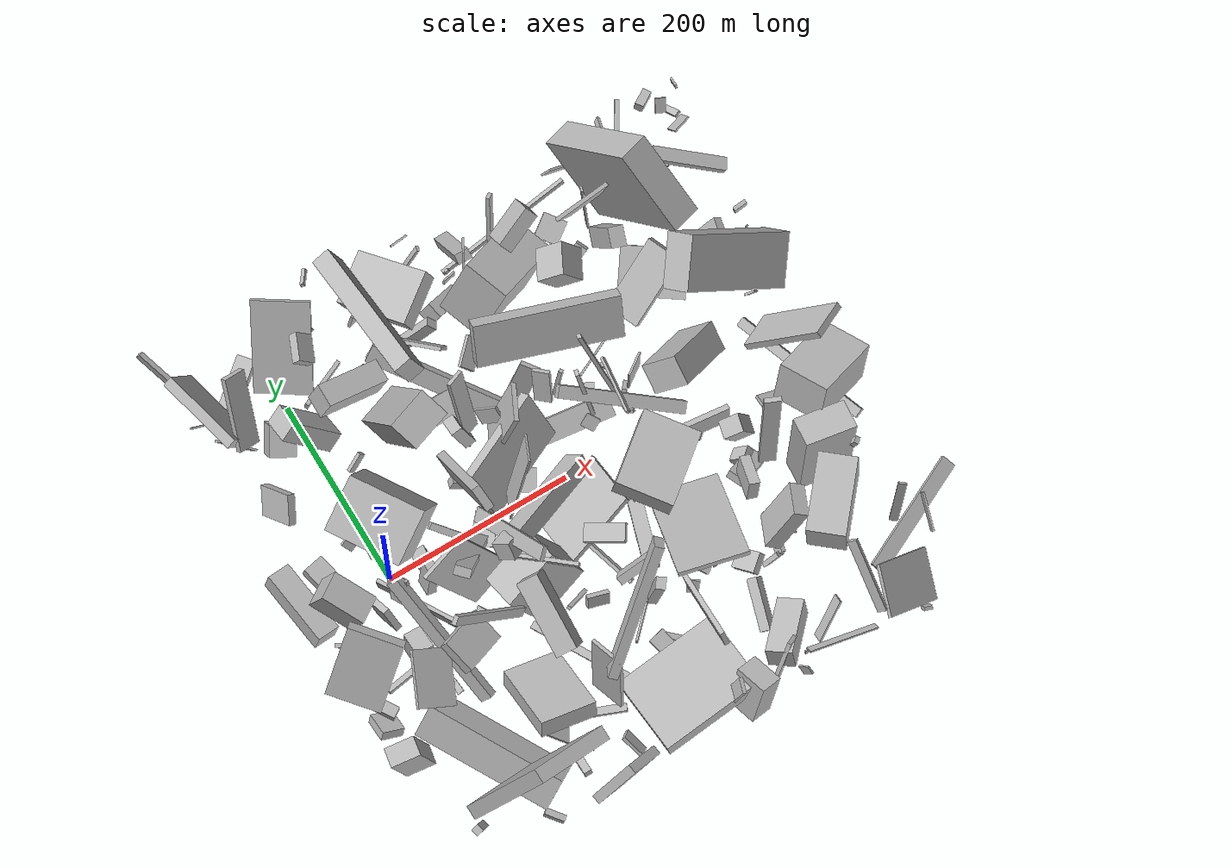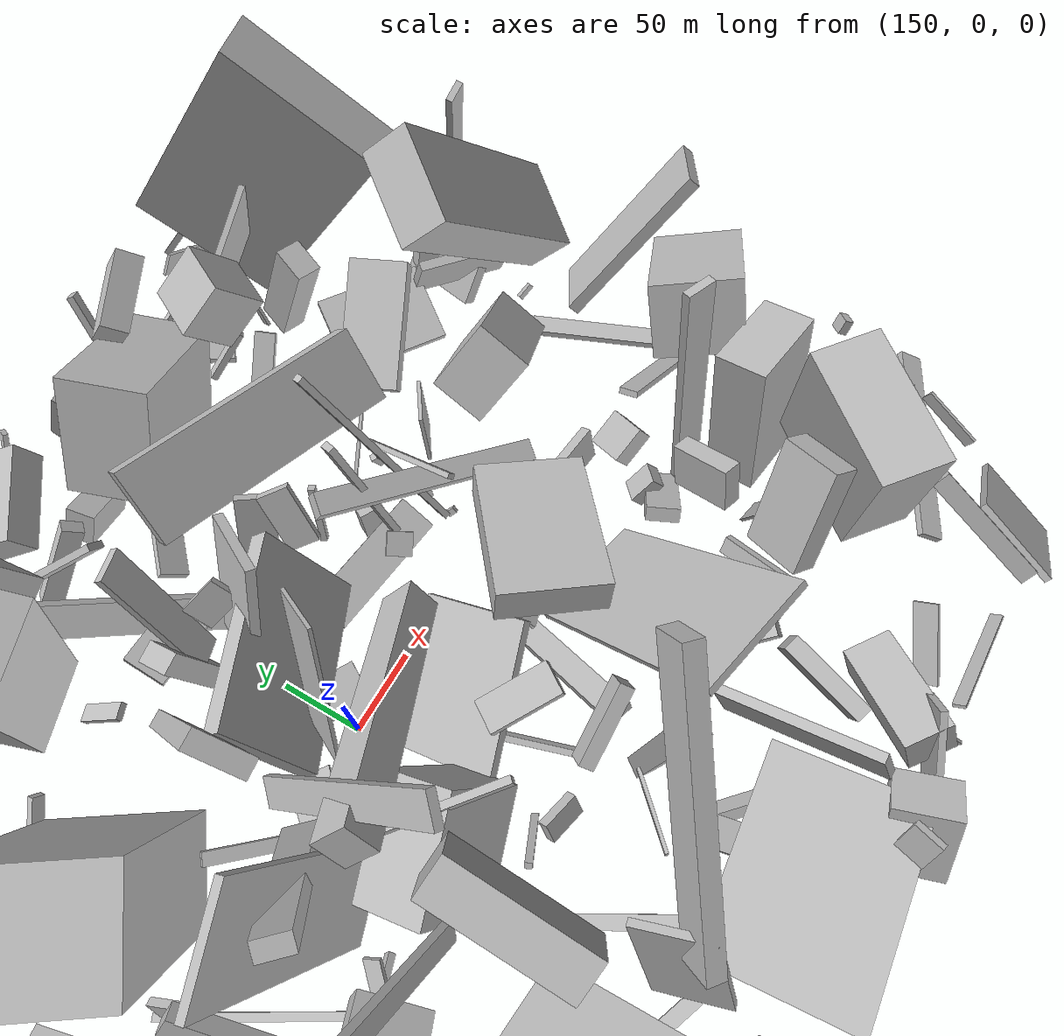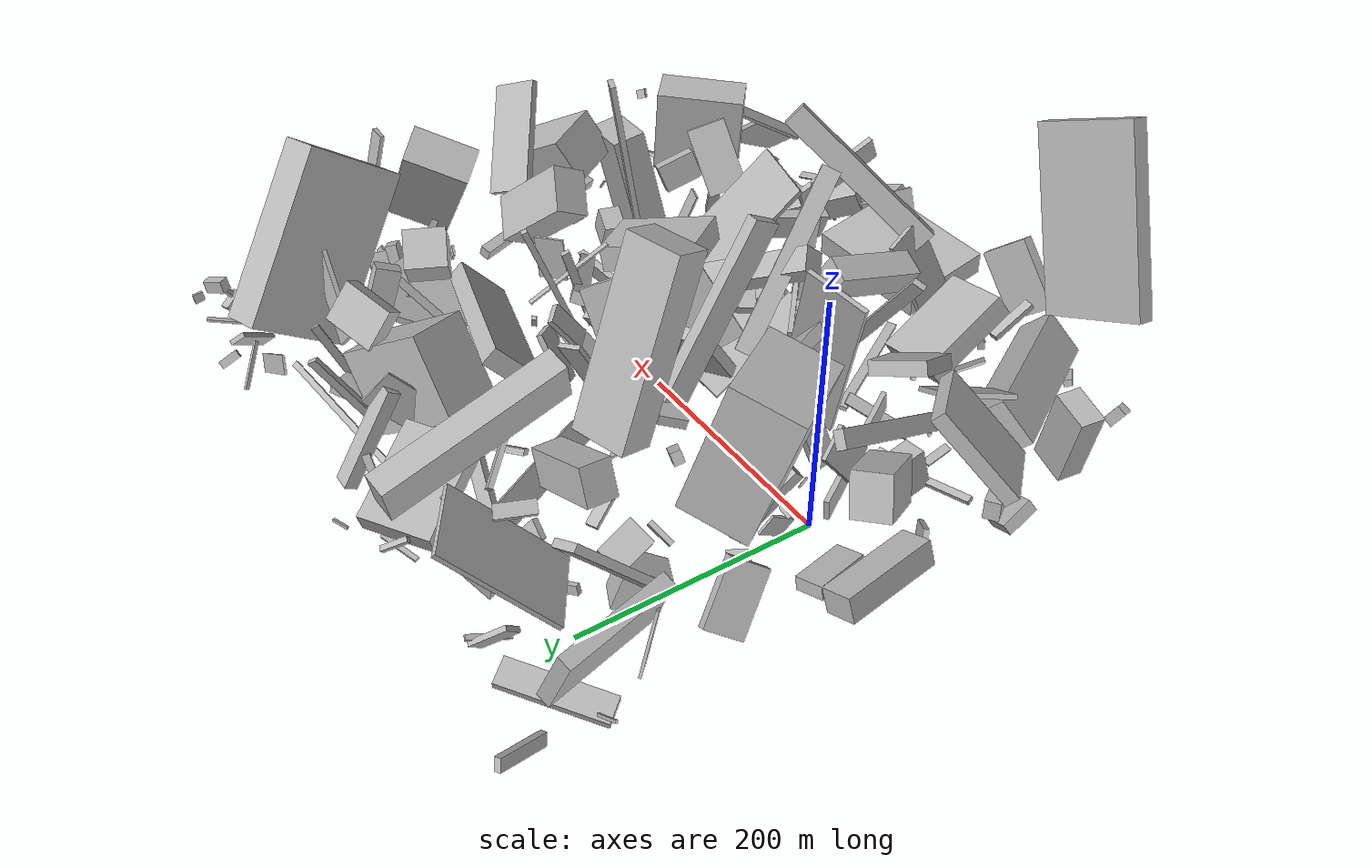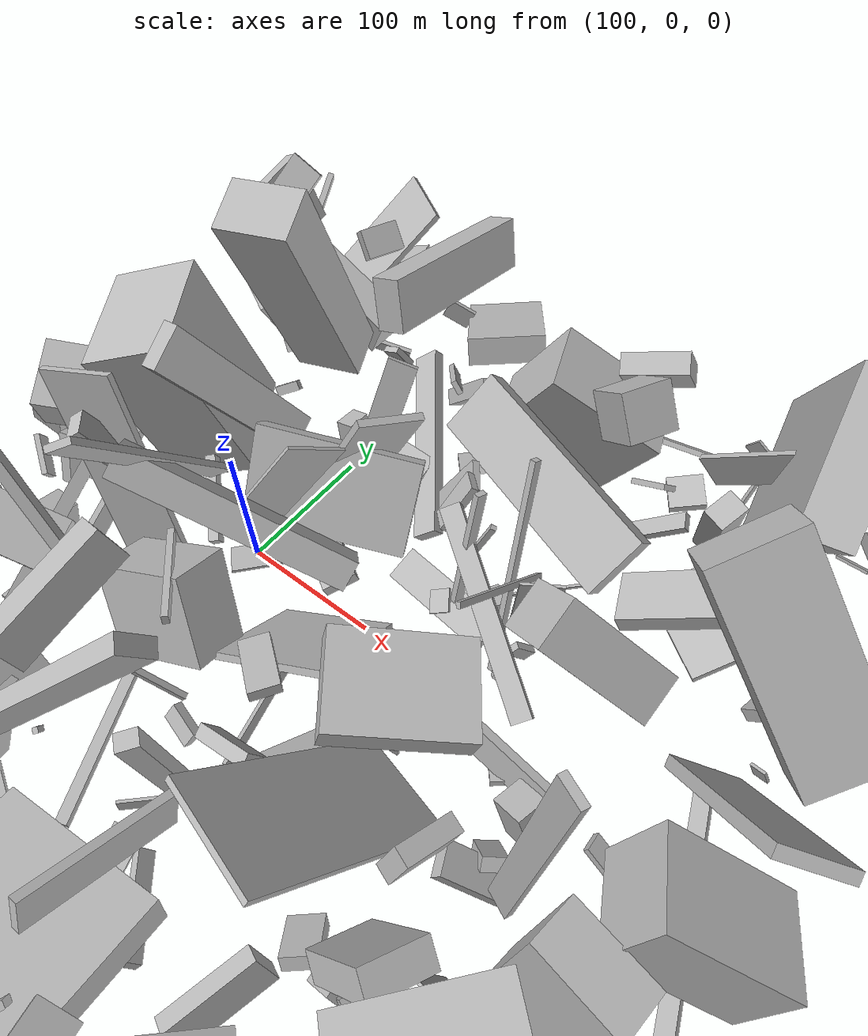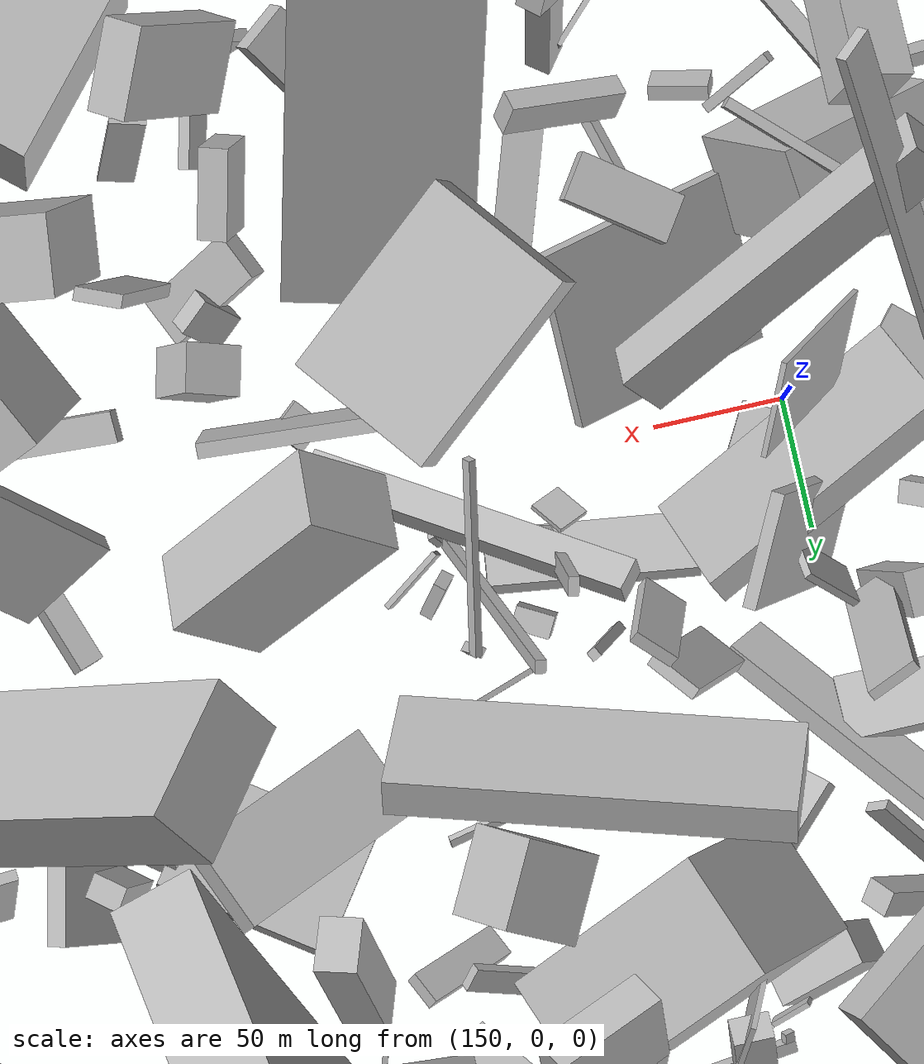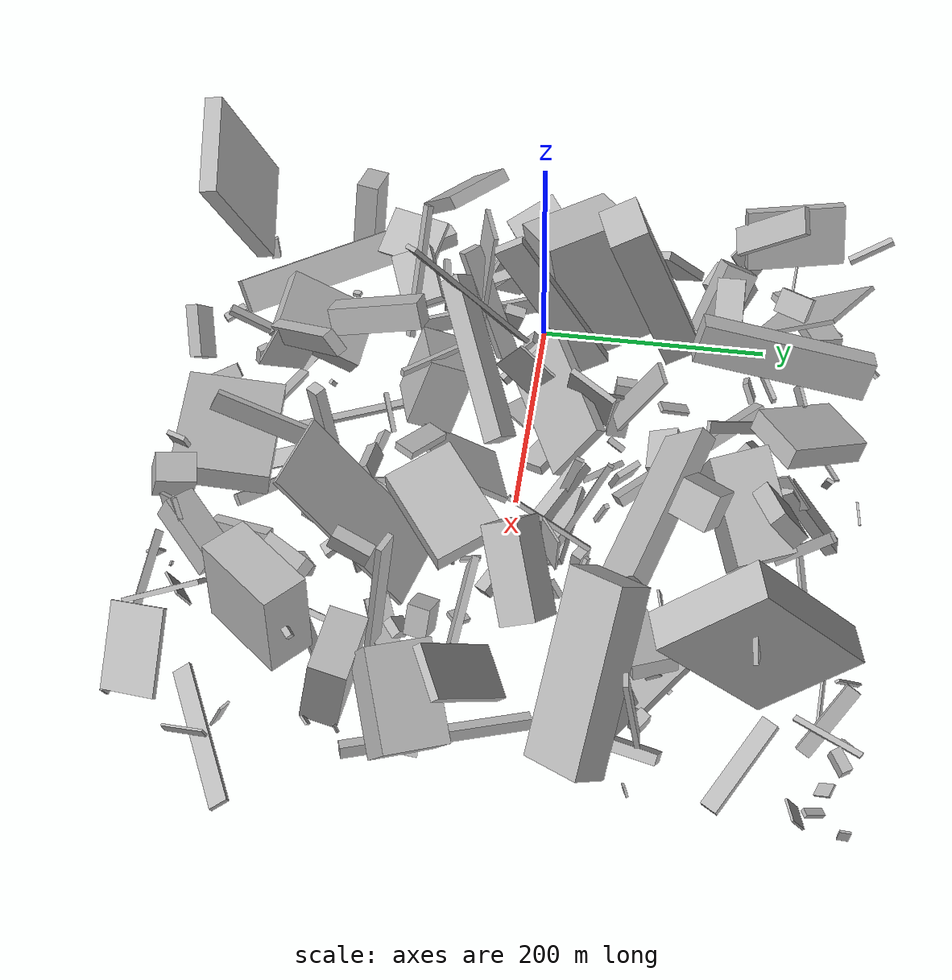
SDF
<sdf version="1.6">
 <world name="default">
  <scene>
   <sky><clouds><speed>12</speed></clouds></sky>
   <ambient>0.4 0.4 0.4 1</ambient>
   <background>0.7 0.7 0.7 1</background>
   <shadows>1</shadows>
  </scene>
  <gravity>0 0 -9.8066</gravity>
  <magnetic_field>6e-06 2.3e-05 -4.2e-05</magnetic_field>
  <physics default="0" name="default_physics" type="ode">
   <ode>
    <solver>
     <type>quick</type>
     <iters>10</iters>
     <sor>1.0</sor>
     <use_dynamic_moi_rescaling>0</use_dynamic_moi_rescaling>
    </solver>
    <constraints>
     <cfm>0</cfm>
     <erp>0.2</erp>
     <contact_max_correcting_vel>100</contact_max_correcting_vel>
     <contact_surface_layer>0.001</contact_surface_layer>
    </constraints>
   </ode>
   <max_step_size>0.004</max_step_size>
   <real_time_factor>1</real_time_factor>
   <real_time_update_rate>250</real_time_update_rate>
  </physics>
  <light name="sun" type="directional">
   <pose>0 0 10 0 0 0</pose>
   <diffuse>0.8 0.8 0.8 1</diffuse>
   <specular>0.2 0.2 0.2 1</specular>
   <attenuation>
    <range>1000</range>
    <constant>0.9</constant>
    <linear>0.01</linear>
    <quadratic>0.001</quadratic>
   </attenuation>
   <direction>-0.5 0.1 -0.9</direction>
  </light>
  <model name="building_1">
   <static>0</static>
   <pose>159.1138077239486 13.436275596271237 57.94684103337113 0.5857820949794299 -0.13775131169422156 -2.6791968526474874</pose>
   <link name="link">
    <gravity>0</gravity>
    <pose>0 0 31.5 0 0 0</pose>
    <collision name="collision"><geometry><box><size>105 10 63</size></box></geometry></collision>
    <visual name="visual">
     <cast_shadows>0</cast_shadows>
     <geometry><box><size>105 10 63</size></box></geometry>
     <material>
      <script>
       <uri>model://HANNAS_wall/materials/scripts</uri>
       <uri>model://HANNAS_wall/materials/textures</uri>
       <name>vrc/HANNAS_wall</name>
      </script>
     </material>
    </visual>
   </link>
  </model>
  <model name="building_2">
   <static>0</static>
   <pose>418.1181025435239 64.45660811479848 94.56265195351862 1.0057984283466672 -0.8061323880651381 2.9371644983583636</pose>
   <link name="link">
    <gravity>0</gravity>
    <pose>0 0 28.0 0 0 0</pose>
    <collision name="collision"><geometry><box><size>150 31 56</size></box></geometry></collision>
    <visual name="visual">
     <cast_shadows>0</cast_shadows>
     <geometry><box><size>150 31 56</size></box></geometry>
     <material>
      <script>
       <uri>model://HANNAS_wall/materials/scripts</uri>
       <uri>model://HANNAS_wall/materials/textures</uri>
       <name>vrc/HANNAS_wall</name>
      </script>
     </material>
    </visual>
   </link>
  </model>
  <model name="building_3">
   <static>0</static>
   <pose>364.0808417446746 109.86434188710595 18.563318313049802 1.2260027277416212 -0.008536355651800357 2.5323561537483035</pose>
   <link name="link">
    <gravity>0</gravity>
    <pose>0 0 25.0 0 0 0</pose>
    <collision name="collision"><geometry><box><size>68 6 50</size></box></geometry></collision>
    <visual name="visual">
     <cast_shadows>0</cast_shadows>
     <geometry><box><size>68 6 50</size></box></geometry>
     <material>
      <script>
       <uri>model://HANNAS_wall/materials/scripts</uri>
       <uri>model://HANNAS_wall/materials/textures</uri>
       <name>vrc/HANNAS_wall</name>
      </script>
     </material>
    </visual>
   </link>
  </model>
  <model name="building_4">
   <static>0</static>
   <pose>403.8561029460927 214.39094951059397 107.00357033889529 1.4035721772929404 -0.9288006494117517 -1.1532855201001826</pose>
   <link name="link">
    <gravity>0</gravity>
    <pose>0 0 16.0 0 0 0</pose>
    <collision name="collision"><geometry><box><size>150 96 32</size></box></geometry></collision>
    <visual name="visual">
     <cast_shadows>0</cast_shadows>
     <geometry><box><size>150 96 32</size></box></geometry>
     <material>
      <script>
       <uri>model://HANNAS_wall/materials/scripts</uri>
       <uri>model://HANNAS_wall/materials/textures</uri>
       <name>vrc/HANNAS_wall</name>
      </script>
     </material>
    </visual>
   </link>
  </model>
  <model name="building_5">
   <static>0</static>
   <pose>398.93339716877426 -172.08604717186736 64.09622754239716 0.053077538592421564 -0.05921299457504138 -0.7085122933176582</pose>
   <link name="link">
    <gravity>0</gravity>
    <pose>0 0 39.0 0 0 0</pose>
    <collision name="collision"><geometry><box><size>39 78 78</size></box></geometry></collision>
    <visual name="visual">
     <cast_shadows>0</cast_shadows>
     <geometry><box><size>39 78 78</size></box></geometry>
     <material>
      <script>
       <uri>model://HANNAS_wall/materials/scripts</uri>
       <uri>model://HANNAS_wall/materials/textures</uri>
       <name>vrc/HANNAS_wall</name>
      </script>
     </material>
    </visual>
   </link>
  </model>
  <model name="building_6">
   <static>0</static>
   <pose>277.89133051898716 -120.46184297197075 64.45076537489118 0.05452620261090895 -0.7977927970173792 -1.8483691170286245</pose>
   <link name="link">
    <gravity>0</gravity>
    <pose>0 0 2.0 0 0 0</pose>
    <collision name="collision"><geometry><box><size>150 72 4</size></box></geometry></collision>
    <visual name="visual">
     <cast_shadows>0</cast_shadows>
     <geometry><box><size>150 72 4</size></box></geometry>
     <material>
      <script>
       <uri>model://HANNAS_wall/materials/scripts</uri>
       <uri>model://HANNAS_wall/materials/textures</uri>
       <name>vrc/HANNAS_wall</name>
      </script>
     </material>
    </visual>
   </link>
  </model>
  <model name="building_7">
   <static>0</static>
   <pose>446.8017825215225 -29.01620865275066 74.84554168238606 1.1951144042633148 -1.0097940043347784 0.7846490316749425</pose>
   <link name="link">
    <gravity>0</gravity>
    <pose>0 0 26.5 0 0 0</pose>
    <collision name="collision"><geometry><box><size>44 81 53</size></box></geometry></collision>
    <visual name="visual">
     <cast_shadows>0</cast_shadows>
     <geometry><box><size>44 81 53</size></box></geometry>
     <material>
      <script>
       <uri>model://HANNAS_wall/materials/scripts</uri>
       <uri>model://HANNAS_wall/materials/textures</uri>
       <name>vrc/HANNAS_wall</name>
      </script>
     </material>
    </visual>
   </link>
  </model>
  <model name="building_8">
   <static>0</static>
   <pose>0.8456267458583824 205.04773165463388 46.59745783080915 0.8320553202530045 0.07223264959962855 2.5471351509358193</pose>
   <link name="link">
    <gravity>0</gravity>
    <pose>0 0 51.0 0 0 0</pose>
    <collision name="collision"><geometry><box><size>59 4 102</size></box></geometry></collision>
    <visual name="visual">
     <cast_shadows>0</cast_shadows>
     <geometry><box><size>59 4 102</size></box></geometry>
     <material>
      <script>
       <uri>model://HANNAS_wall/materials/scripts</uri>
       <uri>model://HANNAS_wall/materials/textures</uri>
       <name>vrc/HANNAS_wall</name>
      </script>
     </material>
    </visual>
   </link>
  </model>
  <model name="building_9">
   <static>0</static>
   <pose>188.99263234189795 -206.2920974212273 40.88188032204099 -0.5076138377383204 -1.4059636773756938 2.158943388256277</pose>
   <link name="link">
    <gravity>0</gravity>
    <pose>0 0 41.5 0 0 0</pose>
    <collision name="collision"><geometry><box><size>21 111 83</size></box></geometry></collision>
    <visual name="visual">
     <cast_shadows>0</cast_shadows>
     <geometry><box><size>21 111 83</size></box></geometry>
     <material>
      <script>
       <uri>model://HANNAS_wall/materials/scripts</uri>
       <uri>model://HANNAS_wall/materials/textures</uri>
       <name>vrc/HANNAS_wall</name>
      </script>
     </material>
    </visual>
   </link>
  </model>
  <model name="building_10">
   <static>0</static>
   <pose>147.91755249715447 54.46704667792444 71.37544862686053 0.31906890251553727 -0.3345849477050274 2.5776239497814135</pose>
   <link name="link">
    <gravity>0</gravity>
    <pose>0 0 37.0 0 0 0</pose>
    <collision name="collision"><geometry><box><size>5 43 74</size></box></geometry></collision>
    <visual name="visual">
     <cast_shadows>0</cast_shadows>
     <geometry><box><size>5 43 74</size></box></geometry>
     <material>
      <script>
       <uri>model://HANNAS_wall/materials/scripts</uri>
       <uri>model://HANNAS_wall/materials/textures</uri>
       <name>vrc/HANNAS_wall</name>
      </script>
     </material>
    </visual>
   </link>
  </model>
  <model name="building_11">
   <static>0</static>
   <pose>-55.88397061824636 111.2717917238354 40.22627905249582 0.7936065777207628 -0.8385531652404434 -1.1349127744845997</pose>
   <link name="link">
    <gravity>0</gravity>
    <pose>0 0 4.0 0 0 0</pose>
    <collision name="collision"><geometry><box><size>51 31 8</size></box></geometry></collision>
    <visual name="visual">
     <cast_shadows>0</cast_shadows>
     <geometry><box><size>51 31 8</size></box></geometry>
     <material>
      <script>
       <uri>model://HANNAS_wall/materials/scripts</uri>
       <uri>model://HANNAS_wall/materials/textures</uri>
       <name>vrc/HANNAS_wall</name>
      </script>
     </material>
    </visual>
   </link>
  </model>
  <model name="building_12">
   <static>0</static>
   <pose>36.43783945632152 -56.415086707224035 93.39397756460609 1.319394883167001 0.18490135291637388 1.8094403178664418</pose>
   <link name="link">
    <gravity>0</gravity>
    <pose>0 0 26.0 0 0 0</pose>
    <collision name="collision"><geometry><box><size>4 150 52</size></box></geometry></collision>
    <visual name="visual">
     <cast_shadows>0</cast_shadows>
     <geometry><box><size>4 150 52</size></box></geometry>
     <material>
      <script>
       <uri>model://HANNAS_wall/materials/scripts</uri>
       <uri>model://HANNAS_wall/materials/textures</uri>
       <name>vrc/HANNAS_wall</name>
      </script>
     </material>
    </visual>
   </link>
  </model>
  <model name="building_13">
   <static>0</static>
   <pose>4.541242665139622 -199.0029150911518 39.2001053849819 0.11401677543668397 -0.7849685948232833 0.43894558370145736</pose>
   <link name="link">
    <gravity>0</gravity>
    <pose>0 0 15.0 0 0 0</pose>
    <collision name="collision"><geometry><box><size>39 146 30</size></box></geometry></collision>
    <visual name="visual">
     <cast_shadows>0</cast_shadows>
     <geometry><box><size>39 146 30</size></box></geometry>
     <material>
      <script>
       <uri>model://HANNAS_wall/materials/scripts</uri>
       <uri>model://HANNAS_wall/materials/textures</uri>
       <name>vrc/HANNAS_wall</name>
      </script>
     </material>
    </visual>
   </link>
  </model>
  <model name="building_14">
   <static>0</static>
   <pose>95.51483392943211 201.38969245307635 34.242334045749026 1.92727393208681 0.8194639101243145 0.9276658580605425</pose>
   <link name="link">
    <gravity>0</gravity>
    <pose>0 0 75.0 0 0 0</pose>
    <collision name="collision"><geometry><box><size>9 20 150</size></box></geometry></collision>
    <visual name="visual">
     <cast_shadows>0</cast_shadows>
     <geometry><box><size>9 20 150</size></box></geometry>
     <material>
      <script>
       <uri>model://HANNAS_wall/materials/scripts</uri>
       <uri>model://HANNAS_wall/materials/textures</uri>
       <name>vrc/HANNAS_wall</name>
      </script>
     </material>
    </visual>
   </link>
  </model>
  <model name="building_15">
   <static>0</static>
   <pose>74.59313998689322 123.98580256936594 88.67878758578753 -0.06287728880933119 -0.34629753177759953 1.9146610443210994</pose>
   <link name="link">
    <gravity>0</gravity>
    <pose>0 0 75.0 0 0 0</pose>
    <collision name="collision"><geometry><box><size>33 45 150</size></box></geometry></collision>
    <visual name="visual">
     <cast_shadows>0</cast_shadows>
     <geometry><box><size>33 45 150</size></box></geometry>
     <material>
      <script>
       <uri>model://HANNAS_wall/materials/scripts</uri>
       <uri>model://HANNAS_wall/materials/textures</uri>
       <name>vrc/HANNAS_wall</name>
      </script>
     </material>
    </visual>
   </link>
  </model>
  <model name="building_16">
   <static>0</static>
   <pose>319.32174859154327 -229.17555205556266 34.30561464346373 1.198908890928895 -0.25580832159423883 -0.6663575494947207</pose>
   <link name="link">
    <gravity>0</gravity>
    <pose>0 0 31.5 0 0 0</pose>
    <collision name="collision"><geometry><box><size>27 24 63</size></box></geometry></collision>
    <visual name="visual">
     <cast_shadows>0</cast_shadows>
     <geometry><box><size>27 24 63</size></box></geometry>
     <material>
      <script>
       <uri>model://HANNAS_wall/materials/scripts</uri>
       <uri>model://HANNAS_wall/materials/textures</uri>
       <name>vrc/HANNAS_wall</name>
      </script>
     </material>
    </visual>
   </link>
  </model>
  <model name="building_17">
   <static>0</static>
   <pose>288.5825087367174 -22.87796729139152 29.732562379120036 1.999127257364877 -1.2344574712953267 1.0833425770302985</pose>
   <link name="link">
    <gravity>0</gravity>
    <pose>0 0 40.5 0 0 0</pose>
    <collision name="collision"><geometry><box><size>22 6 81</size></box></geometry></collision>
    <visual name="visual">
     <cast_shadows>0</cast_shadows>
     <geometry><box><size>22 6 81</size></box></geometry>
     <material>
      <script>
       <uri>model://HANNAS_wall/materials/scripts</uri>
       <uri>model://HANNAS_wall/materials/textures</uri>
       <name>vrc/HANNAS_wall</name>
      </script>
     </material>
    </visual>
   </link>
  </model>
  <model name="building_18">
   <static>0</static>
   <pose>333.53033341735426 -161.84075177534714 67.94300992617995 -0.4588695776004299 -0.31931231626989753 -1.9994311355210548</pose>
   <link name="link">
    <gravity>0</gravity>
    <pose>0 0 31.5 0 0 0</pose>
    <collision name="collision"><geometry><box><size>35 16 63</size></box></geometry></collision>
    <visual name="visual">
     <cast_shadows>0</cast_shadows>
     <geometry><box><size>35 16 63</size></box></geometry>
     <material>
      <script>
       <uri>model://HANNAS_wall/materials/scripts</uri>
       <uri>model://HANNAS_wall/materials/textures</uri>
       <name>vrc/HANNAS_wall</name>
      </script>
     </material>
    </visual>
   </link>
  </model>
  <model name="building_19">
   <static>0</static>
   <pose>130.17571120895607 -76.24500823772865 95.04811241446001 1.527997702878056 -0.19923877381190633 -0.7321909864977894</pose>
   <link name="link">
    <gravity>0</gravity>
    <pose>0 0 2.0 0 0 0</pose>
    <collision name="collision"><geometry><box><size>71 6 4</size></box></geometry></collision>
    <visual name="visual">
     <cast_shadows>0</cast_shadows>
     <geometry><box><size>71 6 4</size></box></geometry>
     <material>
      <script>
       <uri>model://HANNAS_wall/materials/scripts</uri>
       <uri>model://HANNAS_wall/materials/textures</uri>
       <name>vrc/HANNAS_wall</name>
      </script>
     </material>
    </visual>
   </link>
  </model>
  <model name="building_20">
   <static>0</static>
   <pose>361.27698849981493 -163.45771236694168 31.36450086683428 -0.0886284664640928 0.15902502163076193 2.70741251020081</pose>
   <link name="link">
    <gravity>0</gravity>
    <pose>0 0 20.5 0 0 0</pose>
    <collision name="collision"><geometry><box><size>4 11 41</size></box></geometry></collision>
    <visual name="visual">
     <cast_shadows>0</cast_shadows>
     <geometry><box><size>4 11 41</size></box></geometry>
     <material>
      <script>
       <uri>model://HANNAS_wall/materials/scripts</uri>
       <uri>model://HANNAS_wall/materials/textures</uri>
       <name>vrc/HANNAS_wall</name>
      </script>
     </material>
    </visual>
   </link>
  </model>
  <model name="building_21">
   <static>0</static>
   <pose>-62.54899721045746 220.35935203479772 54.889465916284614 0.017928087220613988 0.401777272994292 -2.8875137946002227</pose>
   <link name="link">
    <gravity>0</gravity>
    <pose>0 0 27.5 0 0 0</pose>
    <collision name="collision"><geometry><box><size>11 89 55</size></box></geometry></collision>
    <visual name="visual">
     <cast_shadows>0</cast_shadows>
     <geometry><box><size>11 89 55</size></box></geometry>
     <material>
      <script>
       <uri>model://HANNAS_wall/materials/scripts</uri>
       <uri>model://HANNAS_wall/materials/textures</uri>
       <name>vrc/HANNAS_wall</name>
      </script>
     </material>
    </visual>
   </link>
  </model>
  <model name="building_22">
   <static>0</static>
   <pose>244.9205272004873 172.23392726519427 66.22969239728597 1.4596909657707953 -0.5499924652152032 -2.722451857031103</pose>
   <link name="link">
    <gravity>0</gravity>
    <pose>0 0 24.5 0 0 0</pose>
    <collision name="collision"><geometry><box><size>89 70 49</size></box></geometry></collision>
    <visual name="visual">
     <cast_shadows>0</cast_shadows>
     <geometry><box><size>89 70 49</size></box></geometry>
     <material>
      <script>
       <uri>model://HANNAS_wall/materials/scripts</uri>
       <uri>model://HANNAS_wall/materials/textures</uri>
       <name>vrc/HANNAS_wall</name>
      </script>
     </material>
    </visual>
   </link>
  </model>
  <model name="building_23">
   <static>0</static>
   <pose>-33.32842596712758 151.8489042872372 49.78965106882918 1.1751729924314984 -0.20513603152566345 2.6920419037199546</pose>
   <link name="link">
    <gravity>0</gravity>
    <pose>0 0 16.0 0 0 0</pose>
    <collision name="collision"><geometry><box><size>27 31 32</size></box></geometry></collision>
    <visual name="visual">
     <cast_shadows>0</cast_shadows>
     <geometry><box><size>27 31 32</size></box></geometry>
     <material>
      <script>
       <uri>model://HANNAS_wall/materials/scripts</uri>
       <uri>model://HANNAS_wall/materials/textures</uri>
       <name>vrc/HANNAS_wall</name>
      </script>
     </material>
    </visual>
   </link>
  </model>
  <model name="building_24">
   <static>0</static>
   <pose>330.13753266415074 -8.532858728943339 47.47595338647352 0.7351437066381752 -1.0852591759691783 -1.3733707639014436</pose>
   <link name="link">
    <gravity>0</gravity>
    <pose>0 0 66.5 0 0 0</pose>
    <collision name="collision"><geometry><box><size>10 13 133</size></box></geometry></collision>
    <visual name="visual">
     <cast_shadows>0</cast_shadows>
     <geometry><box><size>10 13 133</size></box></geometry>
     <material>
      <script>
       <uri>model://HANNAS_wall/materials/scripts</uri>
       <uri>model://HANNAS_wall/materials/textures</uri>
       <name>vrc/HANNAS_wall</name>
      </script>
     </material>
    </visual>
   </link>
  </model>
  <model name="building_25">
   <static>0</static>
   <pose>-75.09184787761521 -161.69758410777274 62.96404291163516 1.5248915138746673 -0.2124035435861753 -0.1542566998762562</pose>
   <link name="link">
    <gravity>0</gravity>
    <pose>0 0 10.0 0 0 0</pose>
    <collision name="collision"><geometry><box><size>31 64 20</size></box></geometry></collision>
    <visual name="visual">
     <cast_shadows>0</cast_shadows>
     <geometry><box><size>31 64 20</size></box></geometry>
     <material>
      <script>
       <uri>model://HANNAS_wall/materials/scripts</uri>
       <uri>model://HANNAS_wall/materials/textures</uri>
       <name>vrc/HANNAS_wall</name>
      </script>
     </material>
    </visual>
   </link>
  </model>
  <model name="building_26">
   <static>0</static>
   <pose>407.57354019639257 119.00521632947942 43.659427252811106 -1.870076257196878 -1.1870575320689802 -1.929313125726697</pose>
   <link name="link">
    <gravity>0</gravity>
    <pose>0 0 31.0 0 0 0</pose>
    <collision name="collision"><geometry><box><size>37 6 62</size></box></geometry></collision>
    <visual name="visual">
     <cast_shadows>0</cast_shadows>
     <geometry><box><size>37 6 62</size></box></geometry>
     <material>
      <script>
       <uri>model://HANNAS_wall/materials/scripts</uri>
       <uri>model://HANNAS_wall/materials/textures</uri>
       <name>vrc/HANNAS_wall</name>
      </script>
     </material>
    </visual>
   </link>
  </model>
  <model name="building_27">
   <static>0</static>
   <pose>87.28413426815335 -106.59786719551991 74.59919010898665 0.41591045670004245 0.5016341774629062 -2.5183528324176296</pose>
   <link name="link">
    <gravity>0</gravity>
    <pose>0 0 57.5 0 0 0</pose>
    <collision name="collision"><geometry><box><size>10 5 115</size></box></geometry></collision>
    <visual name="visual">
     <cast_shadows>0</cast_shadows>
     <geometry><box><size>10 5 115</size></box></geometry>
     <material>
      <script>
       <uri>model://HANNAS_wall/materials/scripts</uri>
       <uri>model://HANNAS_wall/materials/textures</uri>
       <name>vrc/HANNAS_wall</name>
      </script>
     </material>
    </visual>
   </link>
  </model>
  <model name="building_28">
   <static>0</static>
   <pose>404.5821279550789 271.5127762346329 29.86012934640669 2.3938090023363086 -0.5157253441062372 -1.8715965324238144</pose>
   <link name="link">
    <gravity>0</gravity>
    <pose>0 0 2.0 0 0 0</pose>
    <collision name="collision"><geometry><box><size>13 64 4</size></box></geometry></collision>
    <visual name="visual">
     <cast_shadows>0</cast_shadows>
     <geometry><box><size>13 64 4</size></box></geometry>
     <material>
      <script>
       <uri>model://HANNAS_wall/materials/scripts</uri>
       <uri>model://HANNAS_wall/materials/textures</uri>
       <name>vrc/HANNAS_wall</name>
      </script>
     </material>
    </visual>
   </link>
  </model>
  <model name="building_29">
   <static>0</static>
   <pose>211.07696831288553 -125.23237079386973 45.82930065977993 0.7993206545895004 -0.9253238774563639 -2.25636208376925</pose>
   <link name="link">
    <gravity>0</gravity>
    <pose>0 0 4.5 0 0 0</pose>
    <collision name="collision"><geometry><box><size>14 48 9</size></box></geometry></collision>
    <visual name="visual">
     <cast_shadows>0</cast_shadows>
     <geometry><box><size>14 48 9</size></box></geometry>
     <material>
      <script>
       <uri>model://HANNAS_wall/materials/scripts</uri>
       <uri>model://HANNAS_wall/materials/textures</uri>
       <name>vrc/HANNAS_wall</name>
      </script>
     </material>
    </visual>
   </link>
  </model>
  <model name="building_30">
   <static>0</static>
   <pose>323.225175625427 101.03876801558152 67.58350733971054 -1.398069640451177 -0.7681768784037347 1.1598286962647242</pose>
   <link name="link">
    <gravity>0</gravity>
    <pose>0 0 75.0 0 0 0</pose>
    <collision name="collision"><geometry><box><size>46 16 150</size></box></geometry></collision>
    <visual name="visual">
     <cast_shadows>0</cast_shadows>
     <geometry><box><size>46 16 150</size></box></geometry>
     <material>
      <script>
       <uri>model://HANNAS_wall/materials/scripts</uri>
       <uri>model://HANNAS_wall/materials/textures</uri>
       <name>vrc/HANNAS_wall</name>
      </script>
     </material>
    </visual>
   </link>
  </model>
  <model name="building_31">
   <static>0</static>
   <pose>425.29663847870665 -95.95535504548681 54.94689572275863 0.5415639457791298 -1.341833681144645 0.8989096563595798</pose>
   <link name="link">
    <gravity>0</gravity>
    <pose>0 0 15.5 0 0 0</pose>
    <collision name="collision"><geometry><box><size>94 54 31</size></box></geometry></collision>
    <visual name="visual">
     <cast_shadows>0</cast_shadows>
     <geometry><box><size>94 54 31</size></box></geometry>
     <material>
      <script>
       <uri>model://HANNAS_wall/materials/scripts</uri>
       <uri>model://HANNAS_wall/materials/textures</uri>
       <name>vrc/HANNAS_wall</name>
      </script>
     </material>
    </visual>
   </link>
  </model>
  <model name="building_32">
   <static>0</static>
   <pose>117.97321559626538 -216.23568642915737 55.36386230536314 -0.2993002425979143 -0.3253679053886669 -1.2873279627586376</pose>
   <link name="link">
    <gravity>0</gravity>
    <pose>0 0 35.0 0 0 0</pose>
    <collision name="collision"><geometry><box><size>39 4 70</size></box></geometry></collision>
    <visual name="visual">
     <cast_shadows>0</cast_shadows>
     <geometry><box><size>39 4 70</size></box></geometry>
     <material>
      <script>
       <uri>model://HANNAS_wall/materials/scripts</uri>
       <uri>model://HANNAS_wall/materials/textures</uri>
       <name>vrc/HANNAS_wall</name>
      </script>
     </material>
    </visual>
   </link>
  </model>
  <model name="building_33">
   <static>0</static>
   <pose>88.63600559604822 -21.531863901675262 64.27053708664766 -0.008276025826326314 0.5534886278040121 -2.3892258149608083</pose>
   <link name="link">
    <gravity>0</gravity>
    <pose>0 0 50.5 0 0 0</pose>
    <collision name="collision"><geometry><box><size>10 17 101</size></box></geometry></collision>
    <visual name="visual">
     <cast_shadows>0</cast_shadows>
     <geometry><box><size>10 17 101</size></box></geometry>
     <material>
      <script>
       <uri>model://HANNAS_wall/materials/scripts</uri>
       <uri>model://HANNAS_wall/materials/textures</uri>
       <name>vrc/HANNAS_wall</name>
      </script>
     </material>
    </visual>
   </link>
  </model>
  <model name="building_34">
   <static>0</static>
   <pose>261.55904670546846 63.35924424055855 23.710356961548815 -3.004043885474984 -0.029149631793515186 2.6386542376238724</pose>
   <link name="link">
    <gravity>0</gravity>
    <pose>0 0 11.0 0 0 0</pose>
    <collision name="collision"><geometry><box><size>15 9 22</size></box></geometry></collision>
    <visual name="visual">
     <cast_shadows>0</cast_shadows>
     <geometry><box><size>15 9 22</size></box></geometry>
     <material>
      <script>
       <uri>model://HANNAS_wall/materials/scripts</uri>
       <uri>model://HANNAS_wall/materials/textures</uri>
       <name>vrc/HANNAS_wall</name>
      </script>
     </material>
    </visual>
   </link>
  </model>
  <model name="building_35">
   <static>0</static>
   <pose>126.36740090806344 -208.7885408143765 107.23726204996753 0.8593568156778081 -0.2245631139838922 2.4088464889971783</pose>
   <link name="link">
    <gravity>0</gravity>
    <pose>0 0 75.0 0 0 0</pose>
    <collision name="collision"><geometry><box><size>10 20 150</size></box></geometry></collision>
    <visual name="visual">
     <cast_shadows>0</cast_shadows>
     <geometry><box><size>10 20 150</size></box></geometry>
     <material>
      <script>
       <uri>model://HANNAS_wall/materials/scripts</uri>
       <uri>model://HANNAS_wall/materials/textures</uri>
       <name>vrc/HANNAS_wall</name>
      </script>
     </material>
    </visual>
   </link>
  </model>
  <model name="building_36">
   <static>0</static>
   <pose>272.1161114277951 230.01621367510282 97.67326355855936 0.5861079996500301 -0.2797166010450879 0.37863836608252543</pose>
   <link name="link">
    <gravity>0</gravity>
    <pose>0 0 17.0 0 0 0</pose>
    <collision name="collision"><geometry><box><size>44 15 34</size></box></geometry></collision>
    <visual name="visual">
     <cast_shadows>0</cast_shadows>
     <geometry><box><size>44 15 34</size></box></geometry>
     <material>
      <script>
       <uri>model://HANNAS_wall/materials/scripts</uri>
       <uri>model://HANNAS_wall/materials/textures</uri>
       <name>vrc/HANNAS_wall</name>
      </script>
     </material>
    </visual>
   </link>
  </model>
  <model name="building_37">
   <static>0</static>
   <pose>356.9067098350816 186.494702843645 58.79823765795722 2.647999442468573 -1.1828707626302162 -1.3700291173630201</pose>
   <link name="link">
    <gravity>0</gravity>
    <pose>0 0 10.5 0 0 0</pose>
    <collision name="collision"><geometry><box><size>71 16 21</size></box></geometry></collision>
    <visual name="visual">
     <cast_shadows>0</cast_shadows>
     <geometry><box><size>71 16 21</size></box></geometry>
     <material>
      <script>
       <uri>model://HANNAS_wall/materials/scripts</uri>
       <uri>model://HANNAS_wall/materials/textures</uri>
       <name>vrc/HANNAS_wall</name>
      </script>
     </material>
    </visual>
   </link>
  </model>
  <model name="building_38">
   <static>0</static>
   <pose>110.1063743259683 210.01617964693372 95.46091207373397 0.27089373075676376 -0.25752482190596915 -1.50701820132834</pose>
   <link name="link">
    <gravity>0</gravity>
    <pose>0 0 18.0 0 0 0</pose>
    <collision name="collision"><geometry><box><size>150 20 36</size></box></geometry></collision>
    <visual name="visual">
     <cast_shadows>0</cast_shadows>
     <geometry><box><size>150 20 36</size></box></geometry>
     <material>
      <script>
       <uri>model://HANNAS_wall/materials/scripts</uri>
       <uri>model://HANNAS_wall/materials/textures</uri>
       <name>vrc/HANNAS_wall</name>
      </script>
     </material>
    </visual>
   </link>
  </model>
  <model name="building_39">
   <static>0</static>
   <pose>-14.246740028703497 -1.7595349841744223 25.642129952614056 1.4309719046076137 0.02585714252078992 0.5200638740085819</pose>
   <link name="link">
    <gravity>0</gravity>
    <pose>0 0 59.5 0 0 0</pose>
    <collision name="collision"><geometry><box><size>4 19 119</size></box></geometry></collision>
    <visual name="visual">
     <cast_shadows>0</cast_shadows>
     <geometry><box><size>4 19 119</size></box></geometry>
     <material>
      <script>
       <uri>model://HANNAS_wall/materials/scripts</uri>
       <uri>model://HANNAS_wall/materials/textures</uri>
       <name>vrc/HANNAS_wall</name>
      </script>
     </material>
    </visual>
   </link>
  </model>
  <model name="building_40">
   <static>0</static>
   <pose>-5.2343420615912635 72.44874677730962 94.18746307907183 -1.7490813672014913 -1.277176754975238 -2.38886350394899</pose>
   <link name="link">
    <gravity>0</gravity>
    <pose>0 0 39.5 0 0 0</pose>
    <collision name="collision"><geometry><box><size>118 58 79</size></box></geometry></collision>
    <visual name="visual">
     <cast_shadows>0</cast_shadows>
     <geometry><box><size>118 58 79</size></box></geometry>
     <material>
      <script>
       <uri>model://HANNAS_wall/materials/scripts</uri>
       <uri>model://HANNAS_wall/materials/textures</uri>
       <name>vrc/HANNAS_wall</name>
      </script>
     </material>
    </visual>
   </link>
  </model>
  <model name="building_41">
   <static>0</static>
   <pose>155.3689195926294 157.6418422677176 72.3585104152755 2.2055301684032913 0.4228930295385421 -2.1631885921597376</pose>
   <link name="link">
    <gravity>0</gravity>
    <pose>0 0 30.5 0 0 0</pose>
    <collision name="collision"><geometry><box><size>4 10 61</size></box></geometry></collision>
    <visual name="visual">
     <cast_shadows>0</cast_shadows>
     <geometry><box><size>4 10 61</size></box></geometry>
     <material>
      <script>
       <uri>model://HANNAS_wall/materials/scripts</uri>
       <uri>model://HANNAS_wall/materials/textures</uri>
       <name>vrc/HANNAS_wall</name>
      </script>
     </material>
    </visual>
   </link>
  </model>
  <model name="building_42">
   <static>0</static>
   <pose>193.77945801608234 -45.64378292756978 37.53339148126348 0.45912615104211196 -0.5126503913420186 -1.5301564673933794</pose>
   <link name="link">
    <gravity>0</gravity>
    <pose>0 0 2.5 0 0 0</pose>
    <collision name="collision"><geometry><box><size>70 85 5</size></box></geometry></collision>
    <visual name="visual">
     <cast_shadows>0</cast_shadows>
     <geometry><box><size>70 85 5</size></box></geometry>
     <material>
      <script>
       <uri>model://HANNAS_wall/materials/scripts</uri>
       <uri>model://HANNAS_wall/materials/textures</uri>
       <name>vrc/HANNAS_wall</name>
      </script>
     </material>
    </visual>
   </link>
  </model>
  <model name="building_43">
   <static>0</static>
   <pose>99.24863558841241 55.71885716492735 76.25988078761047 -0.07716494437695395 -0.5117853786590906 1.7074327518989423</pose>
   <link name="link">
    <gravity>0</gravity>
    <pose>0 0 75.0 0 0 0</pose>
    <collision name="collision"><geometry><box><size>26 9 150</size></box></geometry></collision>
    <visual name="visual">
     <cast_shadows>0</cast_shadows>
     <geometry><box><size>26 9 150</size></box></geometry>
     <material>
      <script>
       <uri>model://HANNAS_wall/materials/scripts</uri>
       <uri>model://HANNAS_wall/materials/textures</uri>
       <name>vrc/HANNAS_wall</name>
      </script>
     </material>
    </visual>
   </link>
  </model>
  <model name="building_44">
   <static>0</static>
   <pose>213.25054710672995 -91.18977194952929 71.39043652763665 -1.8307228632661856 -0.017757153232347573 0.9810431939619569</pose>
   <link name="link">
    <gravity>0</gravity>
    <pose>0 0 21.0 0 0 0</pose>
    <collision name="collision"><geometry><box><size>19 7 42</size></box></geometry></collision>
    <visual name="visual">
     <cast_shadows>0</cast_shadows>
     <geometry><box><size>19 7 42</size></box></geometry>
     <material>
      <script>
       <uri>model://HANNAS_wall/materials/scripts</uri>
       <uri>model://HANNAS_wall/materials/textures</uri>
       <name>vrc/HANNAS_wall</name>
      </script>
     </material>
    </visual>
   </link>
  </model>
  <model name="building_45">
   <static>0</static>
   <pose>342.5688803798966 -94.63408500859082 96.39320158031114 1.2133950294862976 0.17933079309381014 -0.3144139770064585</pose>
   <link name="link">
    <gravity>0</gravity>
    <pose>0 0 17.0 0 0 0</pose>
    <collision name="collision"><geometry><box><size>11 25 34</size></box></geometry></collision>
    <visual name="visual">
     <cast_shadows>0</cast_shadows>
     <geometry><box><size>11 25 34</size></box></geometry>
     <material>
      <script>
       <uri>model://HANNAS_wall/materials/scripts</uri>
       <uri>model://HANNAS_wall/materials/textures</uri>
       <name>vrc/HANNAS_wall</name>
      </script>
     </material>
    </visual>
   </link>
  </model>
  <model name="building_46">
   <static>0</static>
   <pose>155.00696631999432 -111.8103376263063 23.748299713154537 -0.05401651653189584 -0.8682239029723609 0.4713407362368202</pose>
   <link name="link">
    <gravity>0</gravity>
    <pose>0 0 17.5 0 0 0</pose>
    <collision name="collision"><geometry><box><size>4 4 35</size></box></geometry></collision>
    <visual name="visual">
     <cast_shadows>0</cast_shadows>
     <geometry><box><size>4 4 35</size></box></geometry>
     <material>
      <script>
       <uri>model://HANNAS_wall/materials/scripts</uri>
       <uri>model://HANNAS_wall/materials/textures</uri>
       <name>vrc/HANNAS_wall</name>
      </script>
     </material>
    </visual>
   </link>
  </model>
  <model name="building_47">
   <static>0</static>
   <pose>242.08736020114588 -231.47388122181928 18.5705238201404 1.8186696989000284 0.7934641205331967 -2.1810963785697024</pose>
   <link name="link">
    <gravity>0</gravity>
    <pose>0 0 31.0 0 0 0</pose>
    <collision name="collision"><geometry><box><size>7 10 62</size></box></geometry></collision>
    <visual name="visual">
     <cast_shadows>0</cast_shadows>
     <geometry><box><size>7 10 62</size></box></geometry>
     <material>
      <script>
       <uri>model://HANNAS_wall/materials/scripts</uri>
       <uri>model://HANNAS_wall/materials/textures</uri>
       <name>vrc/HANNAS_wall</name>
      </script>
     </material>
    </visual>
   </link>
  </model>
  <model name="building_48">
   <static>0</static>
   <pose>39.130318747306944 201.6770665501179 18.776030131068193 1.6027151602831762 0.2749880032691475 0.4785035606673193</pose>
   <link name="link">
    <gravity>0</gravity>
    <pose>0 0 2.0 0 0 0</pose>
    <collision name="collision"><geometry><box><size>59 8 4</size></box></geometry></collision>
    <visual name="visual">
     <cast_shadows>0</cast_shadows>
     <geometry><box><size>59 8 4</size></box></geometry>
     <material>
      <script>
       <uri>model://HANNAS_wall/materials/scripts</uri>
       <uri>model://HANNAS_wall/materials/textures</uri>
       <name>vrc/HANNAS_wall</name>
      </script>
     </material>
    </visual>
   </link>
  </model>
  <model name="building_49">
   <static>0</static>
   <pose>250.476381653842 33.68549901590971 45.301711947150764 0.28921600647660817 0.11106529564768042 2.9240986375898834</pose>
   <link name="link">
    <gravity>0</gravity>
    <pose>0 0 41.5 0 0 0</pose>
    <collision name="collision"><geometry><box><size>4 7 83</size></box></geometry></collision>
    <visual name="visual">
     <cast_shadows>0</cast_shadows>
     <geometry><box><size>4 7 83</size></box></geometry>
     <material>
      <script>
       <uri>model://HANNAS_wall/materials/scripts</uri>
       <uri>model://HANNAS_wall/materials/textures</uri>
       <name>vrc/HANNAS_wall</name>
      </script>
     </material>
    </visual>
   </link>
  </model>
  <model name="building_50">
   <static>0</static>
   <pose>-53.64200670265925 -102.94198032306673 96.41009918005673 1.4290139397615746 -0.7865368948294857 -2.332572762505514</pose>
   <link name="link">
    <gravity>0</gravity>
    <pose>0 0 28.5 0 0 0</pose>
    <collision name="collision"><geometry><box><size>12 81 57</size></box></geometry></collision>
    <visual name="visual">
     <cast_shadows>0</cast_shadows>
     <geometry><box><size>12 81 57</size></box></geometry>
     <material>
      <script>
       <uri>model://HANNAS_wall/materials/scripts</uri>
       <uri>model://HANNAS_wall/materials/textures</uri>
       <name>vrc/HANNAS_wall</name>
      </script>
     </material>
    </visual>
   </link>
  </model>
  <model name="building_51">
   <static>0</static>
   <pose>212.75103212722263 -149.86429438285782 69.26694926241689 1.6644634336752917 0.0564111201374724 -0.6366898147852937</pose>
   <link name="link">
    <gravity>0</gravity>
    <pose>0 0 6.0 0 0 0</pose>
    <collision name="collision"><geometry><box><size>10 131 12</size></box></geometry></collision>
    <visual name="visual">
     <cast_shadows>0</cast_shadows>
     <geometry><box><size>10 131 12</size></box></geometry>
     <material>
      <script>
       <uri>model://HANNAS_wall/materials/scripts</uri>
       <uri>model://HANNAS_wall/materials/textures</uri>
       <name>vrc/HANNAS_wall</name>
      </script>
     </material>
    </visual>
   </link>
  </model>
  <model name="building_52">
   <static>0</static>
   <pose>132.15696663987652 -229.1655775874666 9.116641134757423 -2.5685505313746813 -1.4608628108774921 2.172176954010982</pose>
   <link name="link">
    <gravity>0</gravity>
    <pose>0 0 28.5 0 0 0</pose>
    <collision name="collision"><geometry><box><size>6 8 57</size></box></geometry></collision>
    <visual name="visual">
     <cast_shadows>0</cast_shadows>
     <geometry><box><size>6 8 57</size></box></geometry>
     <material>
      <script>
       <uri>model://HANNAS_wall/materials/scripts</uri>
       <uri>model://HANNAS_wall/materials/textures</uri>
       <name>vrc/HANNAS_wall</name>
      </script>
     </material>
    </visual>
   </link>
  </model>
  <model name="building_53">
   <static>0</static>
   <pose>206.85785103577174 -11.070453846829343 90.36278645243243 -0.9409472923766149 0.6418157774248305 2.413458784015558</pose>
   <link name="link">
    <gravity>0</gravity>
    <pose>0 0 71.0 0 0 0</pose>
    <collision name="collision"><geometry><box><size>20 19 142</size></box></geometry></collision>
    <visual name="visual">
     <cast_shadows>0</cast_shadows>
     <geometry><box><size>20 19 142</size></box></geometry>
     <material>
      <script>
       <uri>model://HANNAS_wall/materials/scripts</uri>
       <uri>model://HANNAS_wall/materials/textures</uri>
       <name>vrc/HANNAS_wall</name>
      </script>
     </material>
    </visual>
   </link>
  </model>
  <model name="building_54">
   <static>0</static>
   <pose>-3.0955800666413715 -127.08798240169963 75.23317242375342 0.2874428956834237 -0.9980560095499964 -0.6626357192031521</pose>
   <link name="link">
    <gravity>0</gravity>
    <pose>0 0 21.5 0 0 0</pose>
    <collision name="collision"><geometry><box><size>4 57 43</size></box></geometry></collision>
    <visual name="visual">
     <cast_shadows>0</cast_shadows>
     <geometry><box><size>4 57 43</size></box></geometry>
     <material>
      <script>
       <uri>model://HANNAS_wall/materials/scripts</uri>
       <uri>model://HANNAS_wall/materials/textures</uri>
       <name>vrc/HANNAS_wall</name>
      </script>
     </material>
    </visual>
   </link>
  </model>
  <model name="building_55">
   <static>0</static>
   <pose>300.5109677903312 189.02782427712984 41.85188105733084 0.7468422142055865 -0.4814606211074269 -2.2740795503490476</pose>
   <link name="link">
    <gravity>0</gravity>
    <pose>0 0 2.0 0 0 0</pose>
    <collision name="collision"><geometry><box><size>10 34 4</size></box></geometry></collision>
    <visual name="visual">
     <cast_shadows>0</cast_shadows>
     <geometry><box><size>10 34 4</size></box></geometry>
     <material>
      <script>
       <uri>model://HANNAS_wall/materials/scripts</uri>
       <uri>model://HANNAS_wall/materials/textures</uri>
       <name>vrc/HANNAS_wall</name>
      </script>
     </material>
    </visual>
   </link>
  </model>
  <model name="building_56">
   <static>0</static>
   <pose>276.05834337052374 57.47279952764249 73.65135694069491 -0.5432349753458168 -1.1413832118697873 1.911942385262007</pose>
   <link name="link">
    <gravity>0</gravity>
    <pose>0 0 2.5 0 0 0</pose>
    <collision name="collision"><geometry><box><size>150 4 5</size></box></geometry></collision>
    <visual name="visual">
     <cast_shadows>0</cast_shadows>
     <geometry><box><size>150 4 5</size></box></geometry>
     <material>
      <script>
       <uri>model://HANNAS_wall/materials/scripts</uri>
       <uri>model://HANNAS_wall/materials/textures</uri>
       <name>vrc/HANNAS_wall</name>
      </script>
     </material>
    </visual>
   </link>
  </model>
  <model name="building_57">
   <static>0</static>
   <pose>322.88839613433913 212.52281284206057 11.674106666054005 1.3976113307197062 0.21680288784311463 -2.5254096811277864</pose>
   <link name="link">
    <gravity>0</gravity>
    <pose>0 0 12.5 0 0 0</pose>
    <collision name="collision"><geometry><box><size>26 7 25</size></box></geometry></collision>
    <visual name="visual">
     <cast_shadows>0</cast_shadows>
     <geometry><box><size>26 7 25</size></box></geometry>
     <material>
      <script>
       <uri>model://HANNAS_wall/materials/scripts</uri>
       <uri>model://HANNAS_wall/materials/textures</uri>
       <name>vrc/HANNAS_wall</name>
      </script>
     </material>
    </visual>
   </link>
  </model>
  <model name="building_58">
   <static>0</static>
   <pose>-62.47073913357587 -6.6394530027085095 61.34676620785726 0.19669176704112493 -0.36563890039754615 2.1048771639164974</pose>
   <link name="link">
    <gravity>0</gravity>
    <pose>0 0 17.5 0 0 0</pose>
    <collision name="collision"><geometry><box><size>48 30 35</size></box></geometry></collision>
    <visual name="visual">
     <cast_shadows>0</cast_shadows>
     <geometry><box><size>48 30 35</size></box></geometry>
     <material>
      <script>
       <uri>model://HANNAS_wall/materials/scripts</uri>
       <uri>model://HANNAS_wall/materials/textures</uri>
       <name>vrc/HANNAS_wall</name>
      </script>
     </material>
    </visual>
   </link>
  </model>
  <model name="building_59">
   <static>0</static>
   <pose>451.0306686751191 -3.445324895692803 115.67536266211363 2.5673562346572583 -0.8256312993374127 -0.642959854171915</pose>
   <link name="link">
    <gravity>0</gravity>
    <pose>0 0 3.5 0 0 0</pose>
    <collision name="collision"><geometry><box><size>100 43 7</size></box></geometry></collision>
    <visual name="visual">
     <cast_shadows>0</cast_shadows>
     <geometry><box><size>100 43 7</size></box></geometry>
     <material>
      <script>
       <uri>model://HANNAS_wall/materials/scripts</uri>
       <uri>model://HANNAS_wall/materials/textures</uri>
       <name>vrc/HANNAS_wall</name>
      </script>
     </material>
    </visual>
   </link>
  </model>
  <model name="building_60">
   <static>0</static>
   <pose>136.50997856290607 29.76496117374439 16.045714841082177 -1.5903950927033088 -1.3020181948945997 -2.069221431368545</pose>
   <link name="link">
    <gravity>0</gravity>
    <pose>0 0 20.5 0 0 0</pose>
    <collision name="collision"><geometry><box><size>9 24 41</size></box></geometry></collision>
    <visual name="visual">
     <cast_shadows>0</cast_shadows>
     <geometry><box><size>9 24 41</size></box></geometry>
     <material>
      <script>
       <uri>model://HANNAS_wall/materials/scripts</uri>
       <uri>model://HANNAS_wall/materials/textures</uri>
       <name>vrc/HANNAS_wall</name>
      </script>
     </material>
    </visual>
   </link>
  </model>
  <model name="building_61">
   <static>0</static>
   <pose>326.0074032556513 216.7575021618483 53.38060921887083 -0.835956785471656 0.13861588468721125 -1.551623280331134</pose>
   <link name="link">
    <gravity>0</gravity>
    <pose>0 0 60.0 0 0 0</pose>
    <collision name="collision"><geometry><box><size>4 25 120</size></box></geometry></collision>
    <visual name="visual">
     <cast_shadows>0</cast_shadows>
     <geometry><box><size>4 25 120</size></box></geometry>
     <material>
      <script>
       <uri>model://HANNAS_wall/materials/scripts</uri>
       <uri>model://HANNAS_wall/materials/textures</uri>
       <name>vrc/HANNAS_wall</name>
      </script>
     </material>
    </visual>
   </link>
  </model>
  <model name="building_62">
   <static>0</static>
   <pose>260.082762924574 242.21360140547722 54.44905119770806 -1.9219762422614193 -0.9697753091976056 1.0634385125470156</pose>
   <link name="link">
    <gravity>0</gravity>
    <pose>0 0 2.0 0 0 0</pose>
    <collision name="collision"><geometry><box><size>83 9 4</size></box></geometry></collision>
    <visual name="visual">
     <cast_shadows>0</cast_shadows>
     <geometry><box><size>83 9 4</size></box></geometry>
     <material>
      <script>
       <uri>model://HANNAS_wall/materials/scripts</uri>
       <uri>model://HANNAS_wall/materials/textures</uri>
       <name>vrc/HANNAS_wall</name>
      </script>
     </material>
    </visual>
   </link>
  </model>
  <model name="building_63">
   <static>0</static>
   <pose>453.73490536792485 -27.263702049841044 19.407430162297445 0.3422846071769745 -0.053739199249222505 -1.230569500940477</pose>
   <link name="link">
    <gravity>0</gravity>
    <pose>0 0 5.0 0 0 0</pose>
    <collision name="collision"><geometry><box><size>150 10 10</size></box></geometry></collision>
    <visual name="visual">
     <cast_shadows>0</cast_shadows>
     <geometry><box><size>150 10 10</size></box></geometry>
     <material>
      <script>
       <uri>model://HANNAS_wall/materials/scripts</uri>
       <uri>model://HANNAS_wall/materials/textures</uri>
       <name>vrc/HANNAS_wall</name>
      </script>
     </material>
    </visual>
   </link>
  </model>
  <model name="building_64">
   <static>0</static>
   <pose>74.02458167737079 287.9291570671856 73.24218402000206 0.49057019261513607 -0.4791262449545158 -2.184470831997738</pose>
   <link name="link">
    <gravity>0</gravity>
    <pose>0 0 2.0 0 0 0</pose>
    <collision name="collision"><geometry><box><size>21 4 4</size></box></geometry></collision>
    <visual name="visual">
     <cast_shadows>0</cast_shadows>
     <geometry><box><size>21 4 4</size></box></geometry>
     <material>
      <script>
       <uri>model://HANNAS_wall/materials/scripts</uri>
       <uri>model://HANNAS_wall/materials/textures</uri>
       <name>vrc/HANNAS_wall</name>
      </script>
     </material>
    </visual>
   </link>
  </model>
  <model name="building_65">
   <static>0</static>
   <pose>149.81216365987567 101.02048200170125 82.34213266399598 1.2843769817831272 -0.38742513664859834 -1.0593017840155667</pose>
   <link name="link">
    <gravity>0</gravity>
    <pose>0 0 10.0 0 0 0</pose>
    <collision name="collision"><geometry><box><size>4 81 20</size></box></geometry></collision>
    <visual name="visual">
     <cast_shadows>0</cast_shadows>
     <geometry><box><size>4 81 20</size></box></geometry>
     <material>
      <script>
       <uri>model://HANNAS_wall/materials/scripts</uri>
       <uri>model://HANNAS_wall/materials/textures</uri>
       <name>vrc/HANNAS_wall</name>
      </script>
     </material>
    </visual>
   </link>
  </model>
  <model name="building_66">
   <static>0</static>
   <pose>424.6875087127726 -270.5419792257908 54.790916855699294 2.7184363878509337 -0.6679968742944132 3.1196332850886654</pose>
   <link name="link">
    <gravity>0</gravity>
    <pose>0 0 2.0 0 0 0</pose>
    <collision name="collision"><geometry><box><size>70 53 4</size></box></geometry></collision>
    <visual name="visual">
     <cast_shadows>0</cast_shadows>
     <geometry><box><size>70 53 4</size></box></geometry>
     <material>
      <script>
       <uri>model://HANNAS_wall/materials/scripts</uri>
       <uri>model://HANNAS_wall/materials/textures</uri>
       <name>vrc/HANNAS_wall</name>
      </script>
     </material>
    </visual>
   </link>
  </model>
  <model name="building_67">
   <static>0</static>
   <pose>447.1490404149378 117.54538135454116 20.09925021784553 0.9332979593090194 -0.05213215617519594 -1.7870863824838723</pose>
   <link name="link">
    <gravity>0</gravity>
    <pose>0 0 4.5 0 0 0</pose>
    <collision name="collision"><geometry><box><size>53 35 9</size></box></geometry></collision>
    <visual name="visual">
     <cast_shadows>0</cast_shadows>
     <geometry><box><size>53 35 9</size></box></geometry>
     <material>
      <script>
       <uri>model://HANNAS_wall/materials/scripts</uri>
       <uri>model://HANNAS_wall/materials/textures</uri>
       <name>vrc/HANNAS_wall</name>
      </script>
     </material>
    </visual>
   </link>
  </model>
  <model name="building_68">
   <static>0</static>
   <pose>5.256507655177185 -86.90786178527286 50.413180572393436 2.5207611811496866 0.8307474597293015 2.834807596647406</pose>
   <link name="link">
    <gravity>0</gravity>
    <pose>0 0 4.5 0 0 0</pose>
    <collision name="collision"><geometry><box><size>15 150 9</size></box></geometry></collision>
    <visual name="visual">
     <cast_shadows>0</cast_shadows>
     <geometry><box><size>15 150 9</size></box></geometry>
     <material>
      <script>
       <uri>model://HANNAS_wall/materials/scripts</uri>
       <uri>model://HANNAS_wall/materials/textures</uri>
       <name>vrc/HANNAS_wall</name>
      </script>
     </material>
    </visual>
   </link>
  </model>
  <model name="building_69">
   <static>0</static>
   <pose>381.769206946022 -78.69978151049636 102.30986122253354 1.4184671310479926 0.021604764668450144 -0.39764089660711266</pose>
   <link name="link">
    <gravity>0</gravity>
    <pose>0 0 2.5 0 0 0</pose>
    <collision name="collision"><geometry><box><size>17 150 5</size></box></geometry></collision>
    <visual name="visual">
     <cast_shadows>0</cast_shadows>
     <geometry><box><size>17 150 5</size></box></geometry>
     <material>
      <script>
       <uri>model://HANNAS_wall/materials/scripts</uri>
       <uri>model://HANNAS_wall/materials/textures</uri>
       <name>vrc/HANNAS_wall</name>
      </script>
     </material>
    </visual>
   </link>
  </model>
  <model name="building_70">
   <static>0</static>
   <pose>61.94666622010045 -79.79262355864357 7.14680538453102 1.19831154518635 0.4937904822263501 -1.3992327767689834</pose>
   <link name="link">
    <gravity>0</gravity>
    <pose>0 0 9.5 0 0 0</pose>
    <collision name="collision"><geometry><box><size>4 5 19</size></box></geometry></collision>
    <visual name="visual">
     <cast_shadows>0</cast_shadows>
     <geometry><box><size>4 5 19</size></box></geometry>
     <material>
      <script>
       <uri>model://HANNAS_wall/materials/scripts</uri>
       <uri>model://HANNAS_wall/materials/textures</uri>
       <name>vrc/HANNAS_wall</name>
      </script>
     </material>
    </visual>
   </link>
  </model>
  <model name="building_71">
   <static>0</static>
   <pose>430.3617902914512 -43.596646243928795 26.59536363244081 2.582709025484036 -0.23120286905880444 -1.5397441066318263</pose>
   <link name="link">
    <gravity>0</gravity>
    <pose>0 0 2.0 0 0 0</pose>
    <collision name="collision"><geometry><box><size>12 77 4</size></box></geometry></collision>
    <visual name="visual">
     <cast_shadows>0</cast_shadows>
     <geometry><box><size>12 77 4</size></box></geometry>
     <material>
      <script>
       <uri>model://HANNAS_wall/materials/scripts</uri>
       <uri>model://HANNAS_wall/materials/textures</uri>
       <name>vrc/HANNAS_wall</name>
      </script>
     </material>
    </visual>
   </link>
  </model>
  <model name="building_72">
   <static>0</static>
   <pose>29.969000691003973 111.83026962222709 26.231872469217045 -0.5926963470325117 0.406363705698929 1.7265698815919397</pose>
   <link name="link">
    <gravity>0</gravity>
    <pose>0 0 3.5 0 0 0</pose>
    <collision name="collision"><geometry><box><size>4 22 7</size></box></geometry></collision>
    <visual name="visual">
     <cast_shadows>0</cast_shadows>
     <geometry><box><size>4 22 7</size></box></geometry>
     <material>
      <script>
       <uri>model://HANNAS_wall/materials/scripts</uri>
       <uri>model://HANNAS_wall/materials/textures</uri>
       <name>vrc/HANNAS_wall</name>
      </script>
     </material>
    </visual>
   </link>
  </model>
  <model name="building_73">
   <static>0</static>
   <pose>477.1216768093607 122.54973507126299 117.9457586448044 1.7500136691367127 0.1706295868028579 -1.468198586337506</pose>
   <link name="link">
    <gravity>0</gravity>
    <pose>0 0 7.0 0 0 0</pose>
    <collision name="collision"><geometry><box><size>4 65 14</size></box></geometry></collision>
    <visual name="visual">
     <cast_shadows>0</cast_shadows>
     <geometry><box><size>4 65 14</size></box></geometry>
     <material>
      <script>
       <uri>model://HANNAS_wall/materials/scripts</uri>
       <uri>model://HANNAS_wall/materials/textures</uri>
       <name>vrc/HANNAS_wall</name>
      </script>
     </material>
    </visual>
   </link>
  </model>
  <model name="building_74">
   <static>0</static>
   <pose>216.35362475955546 -278.1484164247691 43.41698530253619 -0.230526473746525 -1.1800280516222121 -0.08691773900555856</pose>
   <link name="link">
    <gravity>0</gravity>
    <pose>0 0 2.0 0 0 0</pose>
    <collision name="collision"><geometry><box><size>83 16 4</size></box></geometry></collision>
    <visual name="visual">
     <cast_shadows>0</cast_shadows>
     <geometry><box><size>83 16 4</size></box></geometry>
     <material>
      <script>
       <uri>model://HANNAS_wall/materials/scripts</uri>
       <uri>model://HANNAS_wall/materials/textures</uri>
       <name>vrc/HANNAS_wall</name>
      </script>
     </material>
    </visual>
   </link>
  </model>
  <model name="building_75">
   <static>0</static>
   <pose>274.6693419985804 245.17745441577702 22.295829469117688 0.5603903265473243 0.08965228849764416 -3.0242732265867995</pose>
   <link name="link">
    <gravity>0</gravity>
    <pose>0 0 2.0 0 0 0</pose>
    <collision name="collision"><geometry><box><size>150 5 4</size></box></geometry></collision>
    <visual name="visual">
     <cast_shadows>0</cast_shadows>
     <geometry><box><size>150 5 4</size></box></geometry>
     <material>
      <script>
       <uri>model://HANNAS_wall/materials/scripts</uri>
       <uri>model://HANNAS_wall/materials/textures</uri>
       <name>vrc/HANNAS_wall</name>
      </script>
     </material>
    </visual>
   </link>
  </model>
  <model name="building_76">
   <static>0</static>
   <pose>17.440740557578984 36.93739647670927 10.958492158398693 0.1082173412974126 0.1743827232577553 1.82238035404539</pose>
   <link name="link">
    <gravity>0</gravity>
    <pose>0 0 6.5 0 0 0</pose>
    <collision name="collision"><geometry><box><size>46 11 13</size></box></geometry></collision>
    <visual name="visual">
     <cast_shadows>0</cast_shadows>
     <geometry><box><size>46 11 13</size></box></geometry>
     <material>
      <script>
       <uri>model://HANNAS_wall/materials/scripts</uri>
       <uri>model://HANNAS_wall/materials/textures</uri>
       <name>vrc/HANNAS_wall</name>
      </script>
     </material>
    </visual>
   </link>
  </model>
  <model name="building_77">
   <static>0</static>
   <pose>-5.393950789484571 -35.39091506603029 46.39335104903714 0.5897408686049146 -0.3733254905814361 -2.954361127344352</pose>
   <link name="link">
    <gravity>0</gravity>
    <pose>0 0 17.0 0 0 0</pose>
    <collision name="collision"><geometry><box><size>4 29 34</size></box></geometry></collision>
    <visual name="visual">
     <cast_shadows>0</cast_shadows>
     <geometry><box><size>4 29 34</size></box></geometry>
     <material>
      <script>
       <uri>model://HANNAS_wall/materials/scripts</uri>
       <uri>model://HANNAS_wall/materials/textures</uri>
       <name>vrc/HANNAS_wall</name>
      </script>
     </material>
    </visual>
   </link>
  </model>
  <model name="building_78">
   <static>0</static>
   <pose>-15.572127397359285 -179.11635383153853 12.439783926764356 -1.4617685300752634 -0.018715266342240675 -0.2713216189841278</pose>
   <link name="link">
    <gravity>0</gravity>
    <pose>0 0 3.5 0 0 0</pose>
    <collision name="collision"><geometry><box><size>5 4 7</size></box></geometry></collision>
    <visual name="visual">
     <cast_shadows>0</cast_shadows>
     <geometry><box><size>5 4 7</size></box></geometry>
     <material>
      <script>
       <uri>model://HANNAS_wall/materials/scripts</uri>
       <uri>model://HANNAS_wall/materials/textures</uri>
       <name>vrc/HANNAS_wall</name>
      </script>
     </material>
    </visual>
   </link>
  </model>
  <model name="building_79">
   <static>0</static>
   <pose>150.64885297839666 -207.84983615971902 8.758645481009943 -2.6347344374910953 1.4486290303224207 -0.5579550272427803</pose>
   <link name="link">
    <gravity>0</gravity>
    <pose>0 0 56.5 0 0 0</pose>
    <collision name="collision"><geometry><box><size>4 8 113</size></box></geometry></collision>
    <visual name="visual">
     <cast_shadows>0</cast_shadows>
     <geometry><box><size>4 8 113</size></box></geometry>
     <material>
      <script>
       <uri>model://HANNAS_wall/materials/scripts</uri>
       <uri>model://HANNAS_wall/materials/textures</uri>
       <name>vrc/HANNAS_wall</name>
      </script>
     </material>
    </visual>
   </link>
  </model>
  <model name="building_80">
   <static>0</static>
   <pose>200.64416712637595 100.40076911220166 63.73101889220348 1.761236645236138 0.4646973054681501 0.7625744734293064</pose>
   <link name="link">
    <gravity>0</gravity>
    <pose>0 0 10.5 0 0 0</pose>
    <collision name="collision"><geometry><box><size>5 47 21</size></box></geometry></collision>
    <visual name="visual">
     <cast_shadows>0</cast_shadows>
     <geometry><box><size>5 47 21</size></box></geometry>
     <material>
      <script>
       <uri>model://HANNAS_wall/materials/scripts</uri>
       <uri>model://HANNAS_wall/materials/textures</uri>
       <name>vrc/HANNAS_wall</name>
      </script>
     </material>
    </visual>
   </link>
  </model>
  <model name="building_81">
   <static>0</static>
   <pose>299.7773929217013 -158.85287289773865 18.843176851873803 1.057231121624545 -0.11148352754299828 0.6981386286514321</pose>
   <link name="link">
    <gravity>0</gravity>
    <pose>0 0 13.0 0 0 0</pose>
    <collision name="collision"><geometry><box><size>21 10 26</size></box></geometry></collision>
    <visual name="visual">
     <cast_shadows>0</cast_shadows>
     <geometry><box><size>21 10 26</size></box></geometry>
     <material>
      <script>
       <uri>model://HANNAS_wall/materials/scripts</uri>
       <uri>model://HANNAS_wall/materials/textures</uri>
       <name>vrc/HANNAS_wall</name>
      </script>
     </material>
    </visual>
   </link>
  </model>
  <model name="building_82">
   <static>0</static>
   <pose>86.28270330286712 126.73156508701044 13.718459320199479 -2.6543029003325374 -0.05266108303555212 -2.7326035200266166</pose>
   <link name="link">
    <gravity>0</gravity>
    <pose>0 0 2.0 0 0 0</pose>
    <collision name="collision"><geometry><box><size>10 29 4</size></box></geometry></collision>
    <visual name="visual">
     <cast_shadows>0</cast_shadows>
     <geometry><box><size>10 29 4</size></box></geometry>
     <material>
      <script>
       <uri>model://HANNAS_wall/materials/scripts</uri>
       <uri>model://HANNAS_wall/materials/textures</uri>
       <name>vrc/HANNAS_wall</name>
      </script>
     </material>
    </visual>
   </link>
  </model>
  <model name="building_83">
   <static>0</static>
   <pose>345.881093374061 -156.26535773109475 16.348076535123614 -0.34908434225188595 -0.9855911341040177 0.04418123912363032</pose>
   <link name="link">
    <gravity>0</gravity>
    <pose>0 0 2.5 0 0 0</pose>
    <collision name="collision"><geometry><box><size>11 48 5</size></box></geometry></collision>
    <visual name="visual">
     <cast_shadows>0</cast_shadows>
     <geometry><box><size>11 48 5</size></box></geometry>
     <material>
      <script>
       <uri>model://HANNAS_wall/materials/scripts</uri>
       <uri>model://HANNAS_wall/materials/textures</uri>
       <name>vrc/HANNAS_wall</name>
      </script>
     </material>
    </visual>
   </link>
  </model>
  <model name="building_84">
   <static>0</static>
   <pose>114.95414753383233 -60.92154226704062 47.22754617410052 1.1436150318657143 -0.31716838454540097 0.2866389977388964</pose>
   <link name="link">
    <gravity>0</gravity>
    <pose>0 0 20.0 0 0 0</pose>
    <collision name="collision"><geometry><box><size>64 61 40</size></box></geometry></collision>
    <visual name="visual">
     <cast_shadows>0</cast_shadows>
     <geometry><box><size>64 61 40</size></box></geometry>
     <material>
      <script>
       <uri>model://HANNAS_wall/materials/scripts</uri>
       <uri>model://HANNAS_wall/materials/textures</uri>
       <name>vrc/HANNAS_wall</name>
      </script>
     </material>
    </visual>
   </link>
  </model>
  <model name="building_85">
   <static>0</static>
   <pose>353.11728452761577 -50.1630886402509 45.99892068852472 -0.012615640891261243 -1.0906016608107083 2.910791837761511</pose>
   <link name="link">
    <gravity>0</gravity>
    <pose>0 0 11.0 0 0 0</pose>
    <collision name="collision"><geometry><box><size>27 19 22</size></box></geometry></collision>
    <visual name="visual">
     <cast_shadows>0</cast_shadows>
     <geometry><box><size>27 19 22</size></box></geometry>
     <material>
      <script>
       <uri>model://HANNAS_wall/materials/scripts</uri>
       <uri>model://HANNAS_wall/materials/textures</uri>
       <name>vrc/HANNAS_wall</name>
      </script>
     </material>
    </visual>
   </link>
  </model>
  <model name="building_86">
   <static>0</static>
   <pose>286.84997032534125 67.98352846017391 40.21412783444821 3.024302032379811 -1.1268158244854305 2.5783712227119393</pose>
   <link name="link">
    <gravity>0</gravity>
    <pose>0 0 2.0 0 0 0</pose>
    <collision name="collision"><geometry><box><size>11 4 4</size></box></geometry></collision>
    <visual name="visual">
     <cast_shadows>0</cast_shadows>
     <geometry><box><size>11 4 4</size></box></geometry>
     <material>
      <script>
       <uri>model://HANNAS_wall/materials/scripts</uri>
       <uri>model://HANNAS_wall/materials/textures</uri>
       <name>vrc/HANNAS_wall</name>
      </script>
     </material>
    </visual>
   </link>
  </model>
  <model name="building_87">
   <static>0</static>
   <pose>412.17310957400673 -238.2055836906215 15.408466206727429 -1.5731286308731738 0.4781739315002865 -1.1203410635710378</pose>
   <link name="link">
    <gravity>0</gravity>
    <pose>0 0 65.0 0 0 0</pose>
    <collision name="collision"><geometry><box><size>16 4 130</size></box></geometry></collision>
    <visual name="visual">
     <cast_shadows>0</cast_shadows>
     <geometry><box><size>16 4 130</size></box></geometry>
     <material>
      <script>
       <uri>model://HANNAS_wall/materials/scripts</uri>
       <uri>model://HANNAS_wall/materials/textures</uri>
       <name>vrc/HANNAS_wall</name>
      </script>
     </material>
    </visual>
   </link>
  </model>
  <model name="building_88">
   <static>0</static>
   <pose>74.02712879319677 187.40719494219817 29.891194210743105 -1.1485026055219865 -0.47758147321553773 -0.07082558876759507</pose>
   <link name="link">
    <gravity>0</gravity>
    <pose>0 0 2.5 0 0 0</pose>
    <collision name="collision"><geometry><box><size>16 19 5</size></box></geometry></collision>
    <visual name="visual">
     <cast_shadows>0</cast_shadows>
     <geometry><box><size>16 19 5</size></box></geometry>
     <material>
      <script>
       <uri>model://HANNAS_wall/materials/scripts</uri>
       <uri>model://HANNAS_wall/materials/textures</uri>
       <name>vrc/HANNAS_wall</name>
      </script>
     </material>
    </visual>
   </link>
  </model>
  <model name="building_89">
   <static>0</static>
   <pose>9.570391762079375 254.01672432886105 23.143883656018847 -0.91312683104834 0.7033856679486078 -1.4482992180395065</pose>
   <link name="link">
    <gravity>0</gravity>
    <pose>0 0 2.0 0 0 0</pose>
    <collision name="collision"><geometry><box><size>14 34 4</size></box></geometry></collision>
    <visual name="visual">
     <cast_shadows>0</cast_shadows>
     <geometry><box><size>14 34 4</size></box></geometry>
     <material>
      <script>
       <uri>model://HANNAS_wall/materials/scripts</uri>
       <uri>model://HANNAS_wall/materials/textures</uri>
       <name>vrc/HANNAS_wall</name>
      </script>
     </material>
    </visual>
   </link>
  </model>
  <model name="building_90">
   <static>0</static>
   <pose>187.5624049003038 209.93698805751777 23.630956466309332 -2.6570088056046757 -0.1939682336367444 1.7779496391501863</pose>
   <link name="link">
    <gravity>0</gravity>
    <pose>0 0 11.0 0 0 0</pose>
    <collision name="collision"><geometry><box><size>17 37 22</size></box></geometry></collision>
    <visual name="visual">
     <cast_shadows>0</cast_shadows>
     <geometry><box><size>17 37 22</size></box></geometry>
     <material>
      <script>
       <uri>model://HANNAS_wall/materials/scripts</uri>
       <uri>model://HANNAS_wall/materials/textures</uri>
       <name>vrc/HANNAS_wall</name>
      </script>
     </material>
    </visual>
   </link>
  </model>
  <model name="building_91">
   <static>0</static>
   <pose>50.566517454362064 252.38720608520882 73.54835936217813 -1.8666565423284285 0.12933194364304706 1.8797797809965229</pose>
   <link name="link">
    <gravity>0</gravity>
    <pose>0 0 19.0 0 0 0</pose>
    <collision name="collision"><geometry><box><size>27 11 38</size></box></geometry></collision>
    <visual name="visual">
     <cast_shadows>0</cast_shadows>
     <geometry><box><size>27 11 38</size></box></geometry>
     <material>
      <script>
       <uri>model://HANNAS_wall/materials/scripts</uri>
       <uri>model://HANNAS_wall/materials/textures</uri>
       <name>vrc/HANNAS_wall</name>
      </script>
     </material>
    </visual>
   </link>
  </model>
  <model name="building_92">
   <static>0</static>
   <pose>218.2944240376798 242.84602772322143 41.31008284252313 0.008133346505676034 -1.0307054446017316 -1.580177144983457</pose>
   <link name="link">
    <gravity>0</gravity>
    <pose>0 0 5.5 0 0 0</pose>
    <collision name="collision"><geometry><box><size>85 15 11</size></box></geometry></collision>
    <visual name="visual">
     <cast_shadows>0</cast_shadows>
     <geometry><box><size>85 15 11</size></box></geometry>
     <material>
      <script>
       <uri>model://HANNAS_wall/materials/scripts</uri>
       <uri>model://HANNAS_wall/materials/textures</uri>
       <name>vrc/HANNAS_wall</name>
      </script>
     </material>
    </visual>
   </link>
  </model>
  <model name="building_93">
   <static>0</static>
   <pose>32.38982390780707 -125.629938968056 79.91414015770374 -1.2164814923385863 0.3965378440173269 0.38808967260788607</pose>
   <link name="link">
    <gravity>0</gravity>
    <pose>0 0 18.0 0 0 0</pose>
    <collision name="collision"><geometry><box><size>50 12 36</size></box></geometry></collision>
    <visual name="visual">
     <cast_shadows>0</cast_shadows>
     <geometry><box><size>50 12 36</size></box></geometry>
     <material>
      <script>
       <uri>model://HANNAS_wall/materials/scripts</uri>
       <uri>model://HANNAS_wall/materials/textures</uri>
       <name>vrc/HANNAS_wall</name>
      </script>
     </material>
    </visual>
   </link>
  </model>
  <model name="building_94">
   <static>0</static>
   <pose>237.82640401969547 -266.19479400108986 42.60944343810602 1.1647986920691578 -1.0838434576112543 0.6367862863590698</pose>
   <link name="link">
    <gravity>0</gravity>
    <pose>0 0 17.0 0 0 0</pose>
    <collision name="collision"><geometry><box><size>50 25 34</size></box></geometry></collision>
    <visual name="visual">
     <cast_shadows>0</cast_shadows>
     <geometry><box><size>50 25 34</size></box></geometry>
     <material>
      <script>
       <uri>model://HANNAS_wall/materials/scripts</uri>
       <uri>model://HANNAS_wall/materials/textures</uri>
       <name>vrc/HANNAS_wall</name>
      </script>
     </material>
    </visual>
   </link>
  </model>
  <model name="building_95">
   <static>0</static>
   <pose>213.88296046855135 65.339078772149 62.51630396485814 -0.31799041047845816 0.5861680529979599 0.6203271535672852</pose>
   <link name="link">
    <gravity>0</gravity>
    <pose>0 0 18.0 0 0 0</pose>
    <collision name="collision"><geometry><box><size>5 18 36</size></box></geometry></collision>
    <visual name="visual">
     <cast_shadows>0</cast_shadows>
     <geometry><box><size>5 18 36</size></box></geometry>
     <material>
      <script>
       <uri>model://HANNAS_wall/materials/scripts</uri>
       <uri>model://HANNAS_wall/materials/textures</uri>
       <name>vrc/HANNAS_wall</name>
      </script>
     </material>
    </visual>
   </link>
  </model>
  <model name="building_96">
   <static>0</static>
   <pose>291.9765140608899 -71.24919657547458 78.28093412419483 1.0942737926459882 1.3171638614572745 -2.945131957256762</pose>
   <link name="link">
    <gravity>0</gravity>
    <pose>0 0 30.0 0 0 0</pose>
    <collision name="collision"><geometry><box><size>22 85 60</size></box></geometry></collision>
    <visual name="visual">
     <cast_shadows>0</cast_shadows>
     <geometry><box><size>22 85 60</size></box></geometry>
     <material>
      <script>
       <uri>model://HANNAS_wall/materials/scripts</uri>
       <uri>model://HANNAS_wall/materials/textures</uri>
       <name>vrc/HANNAS_wall</name>
      </script>
     </material>
    </visual>
   </link>
  </model>
  <model name="building_97">
   <static>0</static>
   <pose>97.0037992510102 -6.189766513286463 94.83174843575418 -0.5584461541876407 0.3621641592515689 -2.3894980323687056</pose>
   <link name="link">
    <gravity>0</gravity>
    <pose>0 0 75.0 0 0 0</pose>
    <collision name="collision"><geometry><box><size>15 4 150</size></box></geometry></collision>
    <visual name="visual">
     <cast_shadows>0</cast_shadows>
     <geometry><box><size>15 4 150</size></box></geometry>
     <material>
      <script>
       <uri>model://HANNAS_wall/materials/scripts</uri>
       <uri>model://HANNAS_wall/materials/textures</uri>
       <name>vrc/HANNAS_wall</name>
      </script>
     </material>
    </visual>
   </link>
  </model>
  <model name="building_98">
   <static>0</static>
   <pose>121.06099111650747 -263.7805139013072 28.60274595353453 0.5277088993427566 -0.6980433612679758 -0.04271034023610219</pose>
   <link name="link">
    <gravity>0</gravity>
    <pose>0 0 6.5 0 0 0</pose>
    <collision name="collision"><geometry><box><size>4 26 13</size></box></geometry></collision>
    <visual name="visual">
     <cast_shadows>0</cast_shadows>
     <geometry><box><size>4 26 13</size></box></geometry>
     <material>
      <script>
       <uri>model://HANNAS_wall/materials/scripts</uri>
       <uri>model://HANNAS_wall/materials/textures</uri>
       <name>vrc/HANNAS_wall</name>
      </script>
     </material>
    </visual>
   </link>
  </model>
  <model name="building_99">
   <static>0</static>
   <pose>-19.974798824337938 -252.5264427523147 101.73915300318075 0.41968309603949033 -0.1832129667645532 1.6037552903806749</pose>
   <link name="link">
    <gravity>0</gravity>
    <pose>0 0 75.0 0 0 0</pose>
    <collision name="collision"><geometry><box><size>15 85 150</size></box></geometry></collision>
    <visual name="visual">
     <cast_shadows>0</cast_shadows>
     <geometry><box><size>15 85 150</size></box></geometry>
     <material>
      <script>
       <uri>model://HANNAS_wall/materials/scripts</uri>
       <uri>model://HANNAS_wall/materials/textures</uri>
       <name>vrc/HANNAS_wall</name>
      </script>
     </material>
    </visual>
   </link>
  </model>
  <model name="building_100">
   <static>0</static>
   <pose>230.65425467862158 72.45519883606755 27.57786931816294 0.4017615688648893 0.0593142554362466 2.058509630957529</pose>
   <link name="link">
    <gravity>0</gravity>
    <pose>0 0 19.5 0 0 0</pose>
    <collision name="collision"><geometry><box><size>4 4 39</size></box></geometry></collision>
    <visual name="visual">
     <cast_shadows>0</cast_shadows>
     <geometry><box><size>4 4 39</size></box></geometry>
     <material>
      <script>
       <uri>model://HANNAS_wall/materials/scripts</uri>
       <uri>model://HANNAS_wall/materials/textures</uri>
       <name>vrc/HANNAS_wall</name>
      </script>
     </material>
    </visual>
   </link>
  </model>
  <model name="building_101">
   <static>0</static>
   <pose>90.6085542176134 -177.9893787751117 4.845292110996681 1.904249049998149 0.53871629351348 -0.6276196236221332</pose>
   <link name="link">
    <gravity>0</gravity>
    <pose>0 0 2.0 0 0 0</pose>
    <collision name="collision"><geometry><box><size>4 6 4</size></box></geometry></collision>
    <visual name="visual">
     <cast_shadows>0</cast_shadows>
     <geometry><box><size>4 6 4</size></box></geometry>
     <material>
      <script>
       <uri>model://HANNAS_wall/materials/scripts</uri>
       <uri>model://HANNAS_wall/materials/textures</uri>
       <name>vrc/HANNAS_wall</name>
      </script>
     </material>
    </visual>
   </link>
  </model>
  <model name="building_102">
   <static>0</static>
   <pose>30.552893271594662 222.11640870121983 98.47246167606409 -0.029722519993837647 0.8167771210123939 -0.41773719838884854</pose>
   <link name="link">
    <gravity>0</gravity>
    <pose>0 0 5.0 0 0 0</pose>
    <collision name="collision"><geometry><box><size>21 29 10</size></box></geometry></collision>
    <visual name="visual">
     <cast_shadows>0</cast_shadows>
     <geometry><box><size>21 29 10</size></box></geometry>
     <material>
      <script>
       <uri>model://HANNAS_wall/materials/scripts</uri>
       <uri>model://HANNAS_wall/materials/textures</uri>
       <name>vrc/HANNAS_wall</name>
      </script>
     </material>
    </visual>
   </link>
  </model>
  <model name="building_103">
   <static>0</static>
   <pose>278.8808550957918 -277.7385865037873 48.05843631174262 1.6282387439402446 -0.8151918862577574 -2.6157453657638943</pose>
   <link name="link">
    <gravity>0</gravity>
    <pose>0 0 2.0 0 0 0</pose>
    <collision name="collision"><geometry><box><size>19 62 4</size></box></geometry></collision>
    <visual name="visual">
     <cast_shadows>0</cast_shadows>
     <geometry><box><size>19 62 4</size></box></geometry>
     <material>
      <script>
       <uri>model://HANNAS_wall/materials/scripts</uri>
       <uri>model://HANNAS_wall/materials/textures</uri>
       <name>vrc/HANNAS_wall</name>
      </script>
     </material>
    </visual>
   </link>
  </model>
  <model name="building_104">
   <static>0</static>
   <pose>374.7887703159002 264.73648330415404 28.208678747982198 2.580549788326624 0.146209185974449 -1.6974254747726565</pose>
   <link name="link">
    <gravity>0</gravity>
    <pose>0 0 8.0 0 0 0</pose>
    <collision name="collision"><geometry><box><size>2 80 16</size></box></geometry></collision>
    <visual name="visual">
     <cast_shadows>0</cast_shadows>
     <geometry><box><size>2 80 16</size></box></geometry>
     <material>
      <script>
       <uri>model://HANNAS_wall/materials/scripts</uri>
       <uri>model://HANNAS_wall/materials/textures</uri>
       <name>vrc/HANNAS_wall</name>
      </script>
     </material>
    </visual>
   </link>
  </model>
  <model name="building_105">
   <static>0</static>
   <pose>-70.29775434417392 190.49608712535516 33.95714555498863 0.4291719809812265 -0.1633192740779605 0.7772153757596403</pose>
   <link name="link">
    <gravity>0</gravity>
    <pose>0 0 23.0 0 0 0</pose>
    <collision name="collision"><geometry><box><size>2 30 46</size></box></geometry></collision>
    <visual name="visual">
     <cast_shadows>0</cast_shadows>
     <geometry><box><size>2 30 46</size></box></geometry>
     <material>
      <script>
       <uri>model://HANNAS_wall/materials/scripts</uri>
       <uri>model://HANNAS_wall/materials/textures</uri>
       <name>vrc/HANNAS_wall</name>
      </script>
     </material>
    </visual>
   </link>
  </model>
  <model name="building_106">
   <static>0</static>
   <pose>289.8280359778448 89.972718891993 27.049720409094437 1.579616832089677 0.9185632354323127 0.35698478297060193</pose>
   <link name="link">
    <gravity>0</gravity>
    <pose>0 0 1.0 0 0 0</pose>
    <collision name="collision"><geometry><box><size>2 72 2</size></box></geometry></collision>
    <visual name="visual">
     <cast_shadows>0</cast_shadows>
     <geometry><box><size>2 72 2</size></box></geometry>
     <material>
      <script>
       <uri>model://HANNAS_wall/materials/scripts</uri>
       <uri>model://HANNAS_wall/materials/textures</uri>
       <name>vrc/HANNAS_wall</name>
      </script>
     </material>
    </visual>
   </link>
  </model>
  <model name="building_107">
   <static>0</static>
   <pose>-88.01784358164706 271.43093020198984 40.82976889064575 -0.5514652944964006 -1.0918199617324358 -0.6087742171336732</pose>
   <link name="link">
    <gravity>0</gravity>
    <pose>0 0 21.5 0 0 0</pose>
    <collision name="collision"><geometry><box><size>9 5 43</size></box></geometry></collision>
    <visual name="visual">
     <cast_shadows>0</cast_shadows>
     <geometry><box><size>9 5 43</size></box></geometry>
     <material>
      <script>
       <uri>model://HANNAS_wall/materials/scripts</uri>
       <uri>model://HANNAS_wall/materials/textures</uri>
       <name>vrc/HANNAS_wall</name>
      </script>
     </material>
    </visual>
   </link>
  </model>
  <model name="building_108">
   <static>0</static>
   <pose>-22.16856506814051 -77.6774312852764 27.452258759398823 -1.697097338726337 -0.21162660008305614 -1.540057058186084</pose>
   <link name="link">
    <gravity>0</gravity>
    <pose>0 0 9.5 0 0 0</pose>
    <collision name="collision"><geometry><box><size>25 33 19</size></box></geometry></collision>
    <visual name="visual">
     <cast_shadows>0</cast_shadows>
     <geometry><box><size>25 33 19</size></box></geometry>
     <material>
      <script>
       <uri>model://HANNAS_wall/materials/scripts</uri>
       <uri>model://HANNAS_wall/materials/textures</uri>
       <name>vrc/HANNAS_wall</name>
      </script>
     </material>
    </visual>
   </link>
  </model>
  <model name="building_109">
   <static>0</static>
   <pose>156.05423759919748 78.95990275075366 100.7296975231603 -2.268147272940436 -0.45009740239809 -2.7101574991860913</pose>
   <link name="link">
    <gravity>0</gravity>
    <pose>0 0 8.5 0 0 0</pose>
    <collision name="collision"><geometry><box><size>3 29 17</size></box></geometry></collision>
    <visual name="visual">
     <cast_shadows>0</cast_shadows>
     <geometry><box><size>3 29 17</size></box></geometry>
     <material>
      <script>
       <uri>model://HANNAS_wall/materials/scripts</uri>
       <uri>model://HANNAS_wall/materials/textures</uri>
       <name>vrc/HANNAS_wall</name>
      </script>
     </material>
    </visual>
   </link>
  </model>
  <model name="building_110">
   <static>0</static>
   <pose>413.60405587320264 290.3682700138941 8.853153413269837 0.9092147459898815 0.8273958223171641 -2.6698151261040204</pose>
   <link name="link">
    <gravity>0</gravity>
    <pose>0 0 1.5 0 0 0</pose>
    <collision name="collision"><geometry><box><size>7 18 3</size></box></geometry></collision>
    <visual name="visual">
     <cast_shadows>0</cast_shadows>
     <geometry><box><size>7 18 3</size></box></geometry>
     <material>
      <script>
       <uri>model://HANNAS_wall/materials/scripts</uri>
       <uri>model://HANNAS_wall/materials/textures</uri>
       <name>vrc/HANNAS_wall</name>
      </script>
     </material>
    </visual>
   </link>
  </model>
  <model name="building_111">
   <static>0</static>
   <pose>-64.81422450932719 -123.8154267118015 29.896186390526132 -0.3549209351042798 -1.5048103104821182 -0.6378975023067814</pose>
   <link name="link">
    <gravity>0</gravity>
    <pose>0 0 17.0 0 0 0</pose>
    <collision name="collision"><geometry><box><size>16 12 34</size></box></geometry></collision>
    <visual name="visual">
     <cast_shadows>0</cast_shadows>
     <geometry><box><size>16 12 34</size></box></geometry>
     <material>
      <script>
       <uri>model://HANNAS_wall/materials/scripts</uri>
       <uri>model://HANNAS_wall/materials/textures</uri>
       <name>vrc/HANNAS_wall</name>
      </script>
     </material>
    </visual>
   </link>
  </model>
  <model name="building_112">
   <static>0</static>
   <pose>447.1946653282294 65.42043171356184 12.326869016557088 -0.3201653367893838 -1.0585697678483268 -3.0944324915605126</pose>
   <link name="link">
    <gravity>0</gravity>
    <pose>0 0 5.5 0 0 0</pose>
    <collision name="collision"><geometry><box><size>9 2 11</size></box></geometry></collision>
    <visual name="visual">
     <cast_shadows>0</cast_shadows>
     <geometry><box><size>9 2 11</size></box></geometry>
     <material>
      <script>
       <uri>model://HANNAS_wall/materials/scripts</uri>
       <uri>model://HANNAS_wall/materials/textures</uri>
       <name>vrc/HANNAS_wall</name>
      </script>
     </material>
    </visual>
   </link>
  </model>
  <model name="building_113">
   <static>0</static>
   <pose>119.80440102899865 258.4777780297936 4.724043323899969 -1.3657767329982113 -0.19600121059337325 -1.2033751117268194</pose>
   <link name="link">
    <gravity>0</gravity>
    <pose>0 0 16.5 0 0 0</pose>
    <collision name="collision"><geometry><box><size>4 2 33</size></box></geometry></collision>
    <visual name="visual">
     <cast_shadows>0</cast_shadows>
     <geometry><box><size>4 2 33</size></box></geometry>
     <material>
      <script>
       <uri>model://HANNAS_wall/materials/scripts</uri>
       <uri>model://HANNAS_wall/materials/textures</uri>
       <name>vrc/HANNAS_wall</name>
      </script>
     </material>
    </visual>
   </link>
  </model>
  <model name="building_114">
   <static>0</static>
   <pose>59.19659270159203 165.16837536840458 106.4432731980745 3.109451967350919 -0.4213922808078907 -3.133875041928206</pose>
   <link name="link">
    <gravity>0</gravity>
    <pose>0 0 14.5 0 0 0</pose>
    <collision name="collision"><geometry><box><size>70 24 29</size></box></geometry></collision>
    <visual name="visual">
     <cast_shadows>0</cast_shadows>
     <geometry><box><size>70 24 29</size></box></geometry>
     <material>
      <script>
       <uri>model://HANNAS_wall/materials/scripts</uri>
       <uri>model://HANNAS_wall/materials/textures</uri>
       <name>vrc/HANNAS_wall</name>
      </script>
     </material>
    </visual>
   </link>
  </model>
  <model name="building_115">
   <static>0</static>
   <pose>141.0685982716375 -12.816257305980415 121.86690648148239 2.121806286571211 -0.25320316769243567 2.573996962562446</pose>
   <link name="link">
    <gravity>0</gravity>
    <pose>0 0 18.5 0 0 0</pose>
    <collision name="collision"><geometry><box><size>2 80 37</size></box></geometry></collision>
    <visual name="visual">
     <cast_shadows>0</cast_shadows>
     <geometry><box><size>2 80 37</size></box></geometry>
     <material>
      <script>
       <uri>model://HANNAS_wall/materials/scripts</uri>
       <uri>model://HANNAS_wall/materials/textures</uri>
       <name>vrc/HANNAS_wall</name>
      </script>
     </material>
    </visual>
   </link>
  </model>
  <model name="building_116">
   <static>0</static>
   <pose>15.058156239262946 -286.50752900640816 6.975154273047777 -2.582803474088564 -1.2300198938770073 0.16085480832842552</pose>
   <link name="link">
    <gravity>0</gravity>
    <pose>0 0 3.5 0 0 0</pose>
    <collision name="collision"><geometry><box><size>6 21 7</size></box></geometry></collision>
    <visual name="visual">
     <cast_shadows>0</cast_shadows>
     <geometry><box><size>6 21 7</size></box></geometry>
     <material>
      <script>
       <uri>model://HANNAS_wall/materials/scripts</uri>
       <uri>model://HANNAS_wall/materials/textures</uri>
       <name>vrc/HANNAS_wall</name>
      </script>
     </material>
    </visual>
   </link>
  </model>
  <model name="building_117">
   <static>0</static>
   <pose>390.2570481284121 -248.86937134308366 85.6803238083117 -0.7602898269202253 -0.5635606593788473 1.5063008667648352</pose>
   <link name="link">
    <gravity>0</gravity>
    <pose>0 0 2.0 0 0 0</pose>
    <collision name="collision"><geometry><box><size>80 10 4</size></box></geometry></collision>
    <visual name="visual">
     <cast_shadows>0</cast_shadows>
     <geometry><box><size>80 10 4</size></box></geometry>
     <material>
      <script>
       <uri>model://HANNAS_wall/materials/scripts</uri>
       <uri>model://HANNAS_wall/materials/textures</uri>
       <name>vrc/HANNAS_wall</name>
      </script>
     </material>
    </visual>
   </link>
  </model>
  <model name="building_118">
   <static>0</static>
   <pose>233.30263273342814 -91.688425072378 18.720220214311812 0.3270587146274248 -0.003866870962802843 2.8208815242364316</pose>
   <link name="link">
    <gravity>0</gravity>
    <pose>0 0 3.0 0 0 0</pose>
    <collision name="collision"><geometry><box><size>15 80 6</size></box></geometry></collision>
    <visual name="visual">
     <cast_shadows>0</cast_shadows>
     <geometry><box><size>15 80 6</size></box></geometry>
     <material>
      <script>
       <uri>model://HANNAS_wall/materials/scripts</uri>
       <uri>model://HANNAS_wall/materials/textures</uri>
       <name>vrc/HANNAS_wall</name>
      </script>
     </material>
    </visual>
   </link>
  </model>
  <model name="building_119">
   <static>0</static>
   <pose>141.38216611717172 239.66581618817264 45.167335666899575 -0.39775501628897814 -0.0864841746450626 0.6418341984366717</pose>
   <link name="link">
    <gravity>0</gravity>
    <pose>0 0 10.0 0 0 0</pose>
    <collision name="collision"><geometry><box><size>56 80 20</size></box></geometry></collision>
    <visual name="visual">
     <cast_shadows>0</cast_shadows>
     <geometry><box><size>56 80 20</size></box></geometry>
     <material>
      <script>
       <uri>model://HANNAS_wall/materials/scripts</uri>
       <uri>model://HANNAS_wall/materials/textures</uri>
       <name>vrc/HANNAS_wall</name>
      </script>
     </material>
    </visual>
   </link>
  </model>
  <model name="building_120">
   <static>0</static>
   <pose>481.09202717542223 249.58102824054515 15.451332156293526 -0.9925302986382694 -0.04349892902434185 0.3048485716798019</pose>
   <link name="link">
    <gravity>0</gravity>
    <pose>0 0 1.0 0 0 0</pose>
    <collision name="collision"><geometry><box><size>20 18 2</size></box></geometry></collision>
    <visual name="visual">
     <cast_shadows>0</cast_shadows>
     <geometry><box><size>20 18 2</size></box></geometry>
     <material>
      <script>
       <uri>model://HANNAS_wall/materials/scripts</uri>
       <uri>model://HANNAS_wall/materials/textures</uri>
       <name>vrc/HANNAS_wall</name>
      </script>
     </material>
    </visual>
   </link>
  </model>
  <model name="building_121">
   <static>0</static>
   <pose>348.582311288263 136.15686645702513 8.974284328471684 -0.2168688771877027 1.3011016031371707 -0.4437844545197751</pose>
   <link name="link">
    <gravity>0</gravity>
    <pose>0 0 7.0 0 0 0</pose>
    <collision name="collision"><geometry><box><size>3 14 14</size></box></geometry></collision>
    <visual name="visual">
     <cast_shadows>0</cast_shadows>
     <geometry><box><size>3 14 14</size></box></geometry>
     <material>
      <script>
       <uri>model://HANNAS_wall/materials/scripts</uri>
       <uri>model://HANNAS_wall/materials/textures</uri>
       <name>vrc/HANNAS_wall</name>
      </script>
     </material>
    </visual>
   </link>
  </model>
  <model name="building_122">
   <static>0</static>
   <pose>-76.11204411111744 224.26921811311917 15.73241911171781 1.919742302403753 0.6948824495514917 -0.0806037007722764</pose>
   <link name="link">
    <gravity>0</gravity>
    <pose>0 0 1.0 0 0 0</pose>
    <collision name="collision"><geometry><box><size>46 2 2</size></box></geometry></collision>
    <visual name="visual">
     <cast_shadows>0</cast_shadows>
     <geometry><box><size>46 2 2</size></box></geometry>
     <material>
      <script>
       <uri>model://HANNAS_wall/materials/scripts</uri>
       <uri>model://HANNAS_wall/materials/textures</uri>
       <name>vrc/HANNAS_wall</name>
      </script>
     </material>
    </visual>
   </link>
  </model>
  <model name="building_123">
   <static>0</static>
   <pose>192.82168220112908 222.43306447350756 41.7001417780388 -2.7084369496368166 1.0354870772571019 -2.3105207596886403</pose>
   <link name="link">
    <gravity>0</gravity>
    <pose>0 0 8.5 0 0 0</pose>
    <collision name="collision"><geometry><box><size>5 2 17</size></box></geometry></collision>
    <visual name="visual">
     <cast_shadows>0</cast_shadows>
     <geometry><box><size>5 2 17</size></box></geometry>
     <material>
      <script>
       <uri>model://HANNAS_wall/materials/scripts</uri>
       <uri>model://HANNAS_wall/materials/textures</uri>
       <name>vrc/HANNAS_wall</name>
      </script>
     </material>
    </visual>
   </link>
  </model>
  <model name="building_124">
   <static>0</static>
   <pose>18.262562399465544 149.0394620495764 39.53098936389043 0.5500572608130819 0.5145391659694086 -2.7682685617026817</pose>
   <link name="link">
    <gravity>0</gravity>
    <pose>0 0 32.5 0 0 0</pose>
    <collision name="collision"><geometry><box><size>22 30 65</size></box></geometry></collision>
    <visual name="visual">
     <cast_shadows>0</cast_shadows>
     <geometry><box><size>22 30 65</size></box></geometry>
     <material>
      <script>
       <uri>model://HANNAS_wall/materials/scripts</uri>
       <uri>model://HANNAS_wall/materials/textures</uri>
       <name>vrc/HANNAS_wall</name>
      </script>
     </material>
    </visual>
   </link>
  </model>
  <model name="building_125">
   <static>0</static>
   <pose>144.76065887564476 197.52155302115995 29.343953749855736 1.03523551801513 -0.8182112616976319 -0.17238888059443663</pose>
   <link name="link">
    <gravity>0</gravity>
    <pose>0 0 5.0 0 0 0</pose>
    <collision name="collision"><geometry><box><size>55 12 10</size></box></geometry></collision>
    <visual name="visual">
     <cast_shadows>0</cast_shadows>
     <geometry><box><size>55 12 10</size></box></geometry>
     <material>
      <script>
       <uri>model://HANNAS_wall/materials/scripts</uri>
       <uri>model://HANNAS_wall/materials/textures</uri>
       <name>vrc/HANNAS_wall</name>
      </script>
     </material>
    </visual>
   </link>
  </model>
  <model name="building_126">
   <static>0</static>
   <pose>-58.22047722349818 -51.78536373536729 16.780381469939783 1.0401880805190054 0.1027336624144195 -2.2653221546711206</pose>
   <link name="link">
    <gravity>0</gravity>
    <pose>0 0 15.0 0 0 0</pose>
    <collision name="collision"><geometry><box><size>4 15 30</size></box></geometry></collision>
    <visual name="visual">
     <cast_shadows>0</cast_shadows>
     <geometry><box><size>4 15 30</size></box></geometry>
     <material>
      <script>
       <uri>model://HANNAS_wall/materials/scripts</uri>
       <uri>model://HANNAS_wall/materials/textures</uri>
       <name>vrc/HANNAS_wall</name>
      </script>
     </material>
    </visual>
   </link>
  </model>
  <model name="building_127">
   <static>0</static>
   <pose>308.10255857893844 -272.3179676955249 13.003840421148984 1.819336560177917 0.7632285714518219 1.7041477846618323</pose>
   <link name="link">
    <gravity>0</gravity>
    <pose>0 0 2.0 0 0 0</pose>
    <collision name="collision"><geometry><box><size>2 3 4</size></box></geometry></collision>
    <visual name="visual">
     <cast_shadows>0</cast_shadows>
     <geometry><box><size>2 3 4</size></box></geometry>
     <material>
      <script>
       <uri>model://HANNAS_wall/materials/scripts</uri>
       <uri>model://HANNAS_wall/materials/textures</uri>
       <name>vrc/HANNAS_wall</name>
      </script>
     </material>
    </visual>
   </link>
  </model>
  <model name="building_128">
   <static>0</static>
   <pose>80.34368426141758 -244.83304551099343 15.668406919190724 0.05987941541479943 -0.19570311312839841 -2.3812305642813176</pose>
   <link name="link">
    <gravity>0</gravity>
    <pose>0 0 10.0 0 0 0</pose>
    <collision name="collision"><geometry><box><size>6 10 20</size></box></geometry></collision>
    <visual name="visual">
     <cast_shadows>0</cast_shadows>
     <geometry><box><size>6 10 20</size></box></geometry>
     <material>
      <script>
       <uri>model://HANNAS_wall/materials/scripts</uri>
       <uri>model://HANNAS_wall/materials/textures</uri>
       <name>vrc/HANNAS_wall</name>
      </script>
     </material>
    </visual>
   </link>
  </model>
  <model name="building_129">
   <static>0</static>
   <pose>99.64930429068494 234.55226574974535 58.51166874643939 -1.468062394326968 1.1528407410627628 -2.6635019208187227</pose>
   <link name="link">
    <gravity>0</gravity>
    <pose>0 0 1.5 0 0 0</pose>
    <collision name="collision"><geometry><box><size>16 21 3</size></box></geometry></collision>
    <visual name="visual">
     <cast_shadows>0</cast_shadows>
     <geometry><box><size>16 21 3</size></box></geometry>
     <material>
      <script>
       <uri>model://HANNAS_wall/materials/scripts</uri>
       <uri>model://HANNAS_wall/materials/textures</uri>
       <name>vrc/HANNAS_wall</name>
      </script>
     </material>
    </visual>
   </link>
  </model>
  <model name="building_130">
   <static>0</static>
   <pose>292.52127794680825 -39.69268065906196 28.76807319618768 1.0995985578395517 0.5140523598104639 -1.8290010620625874</pose>
   <link name="link">
    <gravity>0</gravity>
    <pose>0 0 19.5 0 0 0</pose>
    <collision name="collision"><geometry><box><size>2 4 39</size></box></geometry></collision>
    <visual name="visual">
     <cast_shadows>0</cast_shadows>
     <geometry><box><size>2 4 39</size></box></geometry>
     <material>
      <script>
       <uri>model://HANNAS_wall/materials/scripts</uri>
       <uri>model://HANNAS_wall/materials/textures</uri>
       <name>vrc/HANNAS_wall</name>
      </script>
     </material>
    </visual>
   </link>
  </model>
  <model name="building_131">
   <static>0</static>
   <pose>288.6210239560692 -211.30409306012652 34.338914963476455 1.2854848257094322 -0.1574426486896658 1.2885439471627314</pose>
   <link name="link">
    <gravity>0</gravity>
    <pose>0 0 5.0 0 0 0</pose>
    <collision name="collision"><geometry><box><size>53 27 10</size></box></geometry></collision>
    <visual name="visual">
     <cast_shadows>0</cast_shadows>
     <geometry><box><size>53 27 10</size></box></geometry>
     <material>
      <script>
       <uri>model://HANNAS_wall/materials/scripts</uri>
       <uri>model://HANNAS_wall/materials/textures</uri>
       <name>vrc/HANNAS_wall</name>
      </script>
     </material>
    </visual>
   </link>
  </model>
  <model name="building_132">
   <static>0</static>
   <pose>273.4701232428839 -36.072053887656125 10.97615095393935 -1.466966175084831 -0.6755909997459438 0.07695449817707331</pose>
   <link name="link">
    <gravity>0</gravity>
    <pose>0 0 8.5 0 0 0</pose>
    <collision name="collision"><geometry><box><size>13 2 17</size></box></geometry></collision>
    <visual name="visual">
     <cast_shadows>0</cast_shadows>
     <geometry><box><size>13 2 17</size></box></geometry>
     <material>
      <script>
       <uri>model://HANNAS_wall/materials/scripts</uri>
       <uri>model://HANNAS_wall/materials/textures</uri>
       <name>vrc/HANNAS_wall</name>
      </script>
     </material>
    </visual>
   </link>
  </model>
  <model name="building_133">
   <static>0</static>
   <pose>237.96158188177415 23.355411050893103 43.15177517244515 -1.0189314621291563 0.3405139554295601 -0.940038074881489</pose>
   <link name="link">
    <gravity>0</gravity>
    <pose>0 0 7.0 0 0 0</pose>
    <collision name="collision"><geometry><box><size>15 2 14</size></box></geometry></collision>
    <visual name="visual">
     <cast_shadows>0</cast_shadows>
     <geometry><box><size>15 2 14</size></box></geometry>
     <material>
      <script>
       <uri>model://HANNAS_wall/materials/scripts</uri>
       <uri>model://HANNAS_wall/materials/textures</uri>
       <name>vrc/HANNAS_wall</name>
      </script>
     </material>
    </visual>
   </link>
  </model>
  <model name="building_134">
   <static>0</static>
   <pose>314.35318238304166 181.46055903571244 18.444239773644522 2.4719565803867014 -0.13181919791759672 2.0173832704947143</pose>
   <link name="link">
    <gravity>0</gravity>
    <pose>0 0 3.0 0 0 0</pose>
    <collision name="collision"><geometry><box><size>13 42 6</size></box></geometry></collision>
    <visual name="visual">
     <cast_shadows>0</cast_shadows>
     <geometry><box><size>13 42 6</size></box></geometry>
     <material>
      <script>
       <uri>model://HANNAS_wall/materials/scripts</uri>
       <uri>model://HANNAS_wall/materials/textures</uri>
       <name>vrc/HANNAS_wall</name>
      </script>
     </material>
    </visual>
   </link>
  </model>
  <model name="building_135">
   <static>0</static>
   <pose>454.40143197261403 278.4791271784152 50.14925652105803 0.00803775905208576 0.2371428133268745 0.5766942248089305</pose>
   <link name="link">
    <gravity>0</gravity>
    <pose>0 0 5.5 0 0 0</pose>
    <collision name="collision"><geometry><box><size>19 9 11</size></box></geometry></collision>
    <visual name="visual">
     <cast_shadows>0</cast_shadows>
     <geometry><box><size>19 9 11</size></box></geometry>
     <material>
      <script>
       <uri>model://HANNAS_wall/materials/scripts</uri>
       <uri>model://HANNAS_wall/materials/textures</uri>
       <name>vrc/HANNAS_wall</name>
      </script>
     </material>
    </visual>
   </link>
  </model>
  <model name="building_136">
   <static>0</static>
   <pose>103.40681677770371 -168.22778829423567 105.93141304862075 -1.005566578458033 1.080361650588087 0.48768338225531455</pose>
   <link name="link">
    <gravity>0</gravity>
    <pose>0 0 40.0 0 0 0</pose>
    <collision name="collision"><geometry><box><size>24 23 80</size></box></geometry></collision>
    <visual name="visual">
     <cast_shadows>0</cast_shadows>
     <geometry><box><size>24 23 80</size></box></geometry>
     <material>
      <script>
       <uri>model://HANNAS_wall/materials/scripts</uri>
       <uri>model://HANNAS_wall/materials/textures</uri>
       <name>vrc/HANNAS_wall</name>
      </script>
     </material>
    </visual>
   </link>
  </model>
  <model name="building_137">
   <static>0</static>
   <pose>380.4335213487251 -287.06106635700826 22.404067141121956 -1.1063601714961258 0.5731786432905286 1.7124235110476391</pose>
   <link name="link">
    <gravity>0</gravity>
    <pose>0 0 40.0 0 0 0</pose>
    <collision name="collision"><geometry><box><size>7 2 80</size></box></geometry></collision>
    <visual name="visual">
     <cast_shadows>0</cast_shadows>
     <geometry><box><size>7 2 80</size></box></geometry>
     <material>
      <script>
       <uri>model://HANNAS_wall/materials/scripts</uri>
       <uri>model://HANNAS_wall/materials/textures</uri>
       <name>vrc/HANNAS_wall</name>
      </script>
     </material>
    </visual>
   </link>
  </model>
  <model name="building_138">
   <static>0</static>
   <pose>-47.93970931276706 -258.34465054563753 17.369901685136842 -0.11338924852145801 0.490370506443217 -2.960701322171175</pose>
   <link name="link">
    <gravity>0</gravity>
    <pose>0 0 9.0 0 0 0</pose>
    <collision name="collision"><geometry><box><size>9 8 18</size></box></geometry></collision>
    <visual name="visual">
     <cast_shadows>0</cast_shadows>
     <geometry><box><size>9 8 18</size></box></geometry>
     <material>
      <script>
       <uri>model://HANNAS_wall/materials/scripts</uri>
       <uri>model://HANNAS_wall/materials/textures</uri>
       <name>vrc/HANNAS_wall</name>
      </script>
     </material>
    </visual>
   </link>
  </model>
  <model name="building_139">
   <static>0</static>
   <pose>480.6636469605532 -219.17468076940463 40.24567533086979 2.7889607687832783 -0.11224451863660764 2.927083882861287</pose>
   <link name="link">
    <gravity>0</gravity>
    <pose>0 0 4.0 0 0 0</pose>
    <collision name="collision"><geometry><box><size>2 40 8</size></box></geometry></collision>
    <visual name="visual">
     <cast_shadows>0</cast_shadows>
     <geometry><box><size>2 40 8</size></box></geometry>
     <material>
      <script>
       <uri>model://HANNAS_wall/materials/scripts</uri>
       <uri>model://HANNAS_wall/materials/textures</uri>
       <name>vrc/HANNAS_wall</name>
      </script>
     </material>
    </visual>
   </link>
  </model>
  <model name="building_140">
   <static>0</static>
   <pose>68.82470220245824 -153.3009785037837 42.14203907784232 0.4312984984007587 -0.9759398550444025 1.0876894285334808</pose>
   <link name="link">
    <gravity>0</gravity>
    <pose>0 0 40.0 0 0 0</pose>
    <collision name="collision"><geometry><box><size>19 59 80</size></box></geometry></collision>
    <visual name="visual">
     <cast_shadows>0</cast_shadows>
     <geometry><box><size>19 59 80</size></box></geometry>
     <material>
      <script>
       <uri>model://HANNAS_wall/materials/scripts</uri>
       <uri>model://HANNAS_wall/materials/textures</uri>
       <name>vrc/HANNAS_wall</name>
      </script>
     </material>
    </visual>
   </link>
  </model>
  <model name="building_141">
   <static>0</static>
   <pose>74.06600772113903 -2.8635643794584382 42.78223414975423 -0.3871017066126758 0.22962940653903408 -2.4637011726980704</pose>
   <link name="link">
    <gravity>0</gravity>
    <pose>0 0 4.0 0 0 0</pose>
    <collision name="collision"><geometry><box><size>7 60 8</size></box></geometry></collision>
    <visual name="visual">
     <cast_shadows>0</cast_shadows>
     <geometry><box><size>7 60 8</size></box></geometry>
     <material>
      <script>
       <uri>model://HANNAS_wall/materials/scripts</uri>
       <uri>model://HANNAS_wall/materials/textures</uri>
       <name>vrc/HANNAS_wall</name>
      </script>
     </material>
    </visual>
   </link>
  </model>
  <model name="building_142">
   <static>0</static>
   <pose>358.46646447502377 -95.54487240708963 22.31272391759819 1.564124974547798 -0.6345693217902145 -2.7108315550219855</pose>
   <link name="link">
    <gravity>0</gravity>
    <pose>0 0 10.0 0 0 0</pose>
    <collision name="collision"><geometry><box><size>46 9 20</size></box></geometry></collision>
    <visual name="visual">
     <cast_shadows>0</cast_shadows>
     <geometry><box><size>46 9 20</size></box></geometry>
     <material>
      <script>
       <uri>model://HANNAS_wall/materials/scripts</uri>
       <uri>model://HANNAS_wall/materials/textures</uri>
       <name>vrc/HANNAS_wall</name>
      </script>
     </material>
    </visual>
   </link>
  </model>
  <model name="building_143">
   <static>0</static>
   <pose>-1.6446989945058208 77.02518410952128 12.380810744088034 -1.529030485848298 0.2666649139863585 2.5956377665709325</pose>
   <link name="link">
    <gravity>0</gravity>
    <pose>0 0 9.0 0 0 0</pose>
    <collision name="collision"><geometry><box><size>8 4 18</size></box></geometry></collision>
    <visual name="visual">
     <cast_shadows>0</cast_shadows>
     <geometry><box><size>8 4 18</size></box></geometry>
     <material>
      <script>
       <uri>model://HANNAS_wall/materials/scripts</uri>
       <uri>model://HANNAS_wall/materials/textures</uri>
       <name>vrc/HANNAS_wall</name>
      </script>
     </material>
    </visual>
   </link>
  </model>
  <model name="building_144">
   <static>0</static>
   <pose>266.29944410715314 -27.94495326874235 57.40758512810751 2.6852832066774606 1.420002178506908 0.3141649193076575</pose>
   <link name="link">
    <gravity>0</gravity>
    <pose>0 0 4.5 0 0 0</pose>
    <collision name="collision"><geometry><box><size>9 14 9</size></box></geometry></collision>
    <visual name="visual">
     <cast_shadows>0</cast_shadows>
     <geometry><box><size>9 14 9</size></box></geometry>
     <material>
      <script>
       <uri>model://HANNAS_wall/materials/scripts</uri>
       <uri>model://HANNAS_wall/materials/textures</uri>
       <name>vrc/HANNAS_wall</name>
      </script>
     </material>
    </visual>
   </link>
  </model>
  <model name="building_145">
   <static>0</static>
   <pose>373.76941916841065 -141.85198720691625 29.027770643890115 -2.670161785132117 -1.2107980116077968 -2.254730556325783</pose>
   <link name="link">
    <gravity>0</gravity>
    <pose>0 0 1.0 0 0 0</pose>
    <collision name="collision"><geometry><box><size>48 14 2</size></box></geometry></collision>
    <visual name="visual">
     <cast_shadows>0</cast_shadows>
     <geometry><box><size>48 14 2</size></box></geometry>
     <material>
      <script>
       <uri>model://HANNAS_wall/materials/scripts</uri>
       <uri>model://HANNAS_wall/materials/textures</uri>
       <name>vrc/HANNAS_wall</name>
      </script>
     </material>
    </visual>
   </link>
  </model>
  <model name="building_146">
   <static>0</static>
   <pose>479.2039082491084 122.47223037424709 20.78502592028382 1.7570877395378672 -0.6368350375510804 0.3012264547653251</pose>
   <link name="link">
    <gravity>0</gravity>
    <pose>0 0 1.0 0 0 0</pose>
    <collision name="collision"><geometry><box><size>8 9 2</size></box></geometry></collision>
    <visual name="visual">
     <cast_shadows>0</cast_shadows>
     <geometry><box><size>8 9 2</size></box></geometry>
     <material>
      <script>
       <uri>model://HANNAS_wall/materials/scripts</uri>
       <uri>model://HANNAS_wall/materials/textures</uri>
       <name>vrc/HANNAS_wall</name>
      </script>
     </material>
    </visual>
   </link>
  </model>
  <model name="building_147">
   <static>0</static>
   <pose>-49.42987949589588 3.2264163708164233 12.643024851768633 1.3226472070939692 1.3328506367396804 3.1261948083283713</pose>
   <link name="link">
    <gravity>0</gravity>
    <pose>0 0 23.5 0 0 0</pose>
    <collision name="collision"><geometry><box><size>11 23 47</size></box></geometry></collision>
    <visual name="visual">
     <cast_shadows>0</cast_shadows>
     <geometry><box><size>11 23 47</size></box></geometry>
     <material>
      <script>
       <uri>model://HANNAS_wall/materials/scripts</uri>
       <uri>model://HANNAS_wall/materials/textures</uri>
       <name>vrc/HANNAS_wall</name>
      </script>
     </material>
    </visual>
   </link>
  </model>
  <model name="building_148">
   <static>0</static>
   <pose>278.0742966084688 39.436660505235224 80.90513541404212 2.5070053782699944 -0.5222408817465237 0.1702667318581814</pose>
   <link name="link">
    <gravity>0</gravity>
    <pose>0 0 2.0 0 0 0</pose>
    <collision name="collision"><geometry><box><size>3 80 4</size></box></geometry></collision>
    <visual name="visual">
     <cast_shadows>0</cast_shadows>
     <geometry><box><size>3 80 4</size></box></geometry>
     <material>
      <script>
       <uri>model://HANNAS_wall/materials/scripts</uri>
       <uri>model://HANNAS_wall/materials/textures</uri>
       <name>vrc/HANNAS_wall</name>
      </script>
     </material>
    </visual>
   </link>
  </model>
  <model name="building_149">
   <static>0</static>
   <pose>186.67860345044403 149.34464170593657 9.203197228930703 -0.8922509506074872 -0.049624276937482004 0.7892547404301745</pose>
   <link name="link">
    <gravity>0</gravity>
    <pose>0 0 8.5 0 0 0</pose>
    <collision name="collision"><geometry><box><size>33 5 17</size></box></geometry></collision>
    <visual name="visual">
     <cast_shadows>0</cast_shadows>
     <geometry><box><size>33 5 17</size></box></geometry>
     <material>
      <script>
       <uri>model://HANNAS_wall/materials/scripts</uri>
       <uri>model://HANNAS_wall/materials/textures</uri>
       <name>vrc/HANNAS_wall</name>
      </script>
     </material>
    </visual>
   </link>
  </model>
  <model name="building_150">
   <static>0</static>
   <pose>294.1115332642262 172.12026255683486 135.32386553382236 1.5192241176001968 0.8998169292866737 -0.5164920998109009</pose>
   <link name="link">
    <gravity>0</gravity>
    <pose>0 0 16.5 0 0 0</pose>
    <collision name="collision"><geometry><box><size>31 32 33</size></box></geometry></collision>
    <visual name="visual">
     <cast_shadows>0</cast_shadows>
     <geometry><box><size>31 32 33</size></box></geometry>
     <material>
      <script>
       <uri>model://HANNAS_wall/materials/scripts</uri>
       <uri>model://HANNAS_wall/materials/textures</uri>
       <name>vrc/HANNAS_wall</name>
      </script>
     </material>
    </visual>
   </link>
  </model>
  <model name="building_151">
   <static>0</static>
   <pose>291.41289326036207 21.925154391690498 8.01872171182388 2.386913549741348 -0.5088639776181726 -2.8698932512482282</pose>
   <link name="link">
    <gravity>0</gravity>
    <pose>0 0 3.0 0 0 0</pose>
    <collision name="collision"><geometry><box><size>3 4 6</size></box></geometry></collision>
    <visual name="visual">
     <cast_shadows>0</cast_shadows>
     <geometry><box><size>3 4 6</size></box></geometry>
     <material>
      <script>
       <uri>model://HANNAS_wall/materials/scripts</uri>
       <uri>model://HANNAS_wall/materials/textures</uri>
       <name>vrc/HANNAS_wall</name>
      </script>
     </material>
    </visual>
   </link>
  </model>
  <model name="building_152">
   <static>0</static>
   <pose>136.6183285530779 86.40964065652784 8.000514321610828 1.0867661241605875 0.17890787674600692 -0.4369216075596222</pose>
   <link name="link">
    <gravity>0</gravity>
    <pose>0 0 8.0 0 0 0</pose>
    <collision name="collision"><geometry><box><size>6 2 16</size></box></geometry></collision>
    <visual name="visual">
     <cast_shadows>0</cast_shadows>
     <geometry><box><size>6 2 16</size></box></geometry>
     <material>
      <script>
       <uri>model://HANNAS_wall/materials/scripts</uri>
       <uri>model://HANNAS_wall/materials/textures</uri>
       <name>vrc/HANNAS_wall</name>
      </script>
     </material>
    </visual>
   </link>
  </model>
  <model name="building_153">
   <static>0</static>
   <pose>383.55905654196454 131.94612903076634 24.9550853584511 0.2942924624419013 1.0678825533104266 2.140518236021468</pose>
   <link name="link">
    <gravity>0</gravity>
    <pose>0 0 6.0 0 0 0</pose>
    <collision name="collision"><geometry><box><size>25 2 12</size></box></geometry></collision>
    <visual name="visual">
     <cast_shadows>0</cast_shadows>
     <geometry><box><size>25 2 12</size></box></geometry>
     <material>
      <script>
       <uri>model://HANNAS_wall/materials/scripts</uri>
       <uri>model://HANNAS_wall/materials/textures</uri>
       <name>vrc/HANNAS_wall</name>
      </script>
     </material>
    </visual>
   </link>
  </model>
  <model name="building_154">
   <static>0</static>
   <pose>-77.17130345646304 -136.59930092313562 16.664056481490583 -2.1137998256571318 0.446727118337962 -0.22731654057228753</pose>
   <link name="link">
    <gravity>0</gravity>
    <pose>0 0 13.5 0 0 0</pose>
    <collision name="collision"><geometry><box><size>24 10 27</size></box></geometry></collision>
    <visual name="visual">
     <cast_shadows>0</cast_shadows>
     <geometry><box><size>24 10 27</size></box></geometry>
     <material>
      <script>
       <uri>model://HANNAS_wall/materials/scripts</uri>
       <uri>model://HANNAS_wall/materials/textures</uri>
       <name>vrc/HANNAS_wall</name>
      </script>
     </material>
    </visual>
   </link>
  </model>
  <model name="building_155">
   <static>0</static>
   <pose>108.96283075471558 -288.56395107305656 44.48908153487604 0.16038187646957763 -0.8543249615840399 0.03127807475793609</pose>
   <link name="link">
    <gravity>0</gravity>
    <pose>0 0 22.5 0 0 0</pose>
    <collision name="collision"><geometry><box><size>62 10 45</size></box></geometry></collision>
    <visual name="visual">
     <cast_shadows>0</cast_shadows>
     <geometry><box><size>62 10 45</size></box></geometry>
     <material>
      <script>
       <uri>model://HANNAS_wall/materials/scripts</uri>
       <uri>model://HANNAS_wall/materials/textures</uri>
       <name>vrc/HANNAS_wall</name>
      </script>
     </material>
    </visual>
   </link>
  </model>
  <model name="building_156">
   <static>0</static>
   <pose>325.7015556989244 -177.87631841210475 22.347667452457717 2.469586719311925 -0.08529168228660557 1.632691162363394</pose>
   <link name="link">
    <gravity>0</gravity>
    <pose>0 0 6.5 0 0 0</pose>
    <collision name="collision"><geometry><box><size>5 20 13</size></box></geometry></collision>
    <visual name="visual">
     <cast_shadows>0</cast_shadows>
     <geometry><box><size>5 20 13</size></box></geometry>
     <material>
      <script>
       <uri>model://HANNAS_wall/materials/scripts</uri>
       <uri>model://HANNAS_wall/materials/textures</uri>
       <name>vrc/HANNAS_wall</name>
      </script>
     </material>
    </visual>
   </link>
  </model>
  <model name="building_157">
   <static>0</static>
   <pose>300.8638011199498 40.45221302479238 63.41395434358043 0.07656119294501719 0.019401236816475594 2.1927167157829666</pose>
   <link name="link">
    <gravity>0</gravity>
    <pose>0 0 19.5 0 0 0</pose>
    <collision name="collision"><geometry><box><size>2 26 39</size></box></geometry></collision>
    <visual name="visual">
     <cast_shadows>0</cast_shadows>
     <geometry><box><size>2 26 39</size></box></geometry>
     <material>
      <script>
       <uri>model://HANNAS_wall/materials/scripts</uri>
       <uri>model://HANNAS_wall/materials/textures</uri>
       <name>vrc/HANNAS_wall</name>
      </script>
     </material>
    </visual>
   </link>
  </model>
  <model name="building_158">
   <static>0</static>
   <pose>328.7099115369804 106.27358461200646 28.29361405004267 -1.1274236364647996 -0.03023707845062469 -1.1730072623860481</pose>
   <link name="link">
    <gravity>0</gravity>
    <pose>0 0 40.0 0 0 0</pose>
    <collision name="collision"><geometry><box><size>37 12 80</size></box></geometry></collision>
    <visual name="visual">
     <cast_shadows>0</cast_shadows>
     <geometry><box><size>37 12 80</size></box></geometry>
     <material>
      <script>
       <uri>model://HANNAS_wall/materials/scripts</uri>
       <uri>model://HANNAS_wall/materials/textures</uri>
       <name>vrc/HANNAS_wall</name>
      </script>
     </material>
    </visual>
   </link>
  </model>
  <model name="building_159">
   <static>0</static>
   <pose>200.76665908603414 193.51099772725564 39.025450057141335 0.0029726174521645435 -0.8395337526580868 -2.070330284461258</pose>
   <link name="link">
    <gravity>0</gravity>
    <pose>0 0 32.0 0 0 0</pose>
    <collision name="collision"><geometry><box><size>34 2 64</size></box></geometry></collision>
    <visual name="visual">
     <cast_shadows>0</cast_shadows>
     <geometry><box><size>34 2 64</size></box></geometry>
     <material>
      <script>
       <uri>model://HANNAS_wall/materials/scripts</uri>
       <uri>model://HANNAS_wall/materials/textures</uri>
       <name>vrc/HANNAS_wall</name>
      </script>
     </material>
    </visual>
   </link>
  </model>
  <model name="building_160">
   <static>0</static>
   <pose>-23.882730387760784 -42.65525345988743 35.0144166998248 -0.024859701573894607 0.43447777288372597 1.8262634089793355</pose>
   <link name="link">
    <gravity>0</gravity>
    <pose>0 0 18.5 0 0 0</pose>
    <collision name="collision"><geometry><box><size>27 7 37</size></box></geometry></collision>
    <visual name="visual">
     <cast_shadows>0</cast_shadows>
     <geometry><box><size>27 7 37</size></box></geometry>
     <material>
      <script>
       <uri>model://HANNAS_wall/materials/scripts</uri>
       <uri>model://HANNAS_wall/materials/textures</uri>
       <name>vrc/HANNAS_wall</name>
      </script>
     </material>
    </visual>
   </link>
  </model>
  <model name="building_161">
   <static>0</static>
   <pose>356.77305857331237 232.13276831414652 54.036747066376016 -2.7285716019769737 -0.002912268423189879 2.879869655872085</pose>
   <link name="link">
    <gravity>0</gravity>
    <pose>0 0 29.0 0 0 0</pose>
    <collision name="collision"><geometry><box><size>2 7 58</size></box></geometry></collision>
    <visual name="visual">
     <cast_shadows>0</cast_shadows>
     <geometry><box><size>2 7 58</size></box></geometry>
     <material>
      <script>
       <uri>model://HANNAS_wall/materials/scripts</uri>
       <uri>model://HANNAS_wall/materials/textures</uri>
       <name>vrc/HANNAS_wall</name>
      </script>
     </material>
    </visual>
   </link>
  </model>
  <model name="building_162">
   <static>0</static>
   <pose>204.02795934362416 -239.37944293152867 14.994758796985458 1.3600264880968935 -0.12331547867697695 -2.8793720329769585</pose>
   <link name="link">
    <gravity>0</gravity>
    <pose>0 0 28.5 0 0 0</pose>
    <collision name="collision"><geometry><box><size>18 2 57</size></box></geometry></collision>
    <visual name="visual">
     <cast_shadows>0</cast_shadows>
     <geometry><box><size>18 2 57</size></box></geometry>
     <material>
      <script>
       <uri>model://HANNAS_wall/materials/scripts</uri>
       <uri>model://HANNAS_wall/materials/textures</uri>
       <name>vrc/HANNAS_wall</name>
      </script>
     </material>
    </visual>
   </link>
  </model>
  <model name="building_163">
   <static>0</static>
   <pose>53.495085628109386 -199.58266428509793 27.18942992198559 -2.149864519324354 -0.41844656046600415 -2.1313673247878495</pose>
   <link name="link">
    <gravity>0</gravity>
    <pose>0 0 15.5 0 0 0</pose>
    <collision name="collision"><geometry><box><size>33 2 31</size></box></geometry></collision>
    <visual name="visual">
     <cast_shadows>0</cast_shadows>
     <geometry><box><size>33 2 31</size></box></geometry>
     <material>
      <script>
       <uri>model://HANNAS_wall/materials/scripts</uri>
       <uri>model://HANNAS_wall/materials/textures</uri>
       <name>vrc/HANNAS_wall</name>
      </script>
     </material>
    </visual>
   </link>
  </model>
  <model name="building_164">
   <static>0</static>
   <pose>22.506111519393173 -112.19443037733151 20.017216020061802 -0.9967551578518585 -0.494504883868818 -1.1126999780126987</pose>
   <link name="link">
    <gravity>0</gravity>
    <pose>0 0 28.0 0 0 0</pose>
    <collision name="collision"><geometry><box><size>10 2 56</size></box></geometry></collision>
    <visual name="visual">
     <cast_shadows>0</cast_shadows>
     <geometry><box><size>10 2 56</size></box></geometry>
     <material>
      <script>
       <uri>model://HANNAS_wall/materials/scripts</uri>
       <uri>model://HANNAS_wall/materials/textures</uri>
       <name>vrc/HANNAS_wall</name>
      </script>
     </material>
    </visual>
   </link>
  </model>
  <model name="building_165">
   <static>0</static>
   <pose>35.28316622889924 -24.574630991480053 8.130823953308855 -1.476731752308987 -0.48995278389119234 0.421701031083761</pose>
   <link name="link">
    <gravity>0</gravity>
    <pose>0 0 6.5 0 0 0</pose>
    <collision name="collision"><geometry><box><size>2 2 13</size></box></geometry></collision>
    <visual name="visual">
     <cast_shadows>0</cast_shadows>
     <geometry><box><size>2 2 13</size></box></geometry>
     <material>
      <script>
       <uri>model://HANNAS_wall/materials/scripts</uri>
       <uri>model://HANNAS_wall/materials/textures</uri>
       <name>vrc/HANNAS_wall</name>
      </script>
     </material>
    </visual>
   </link>
  </model>
  <model name="building_166">
   <static>0</static>
   <pose>155.3664893102802 120.83708643530599 11.059956710181648 1.4219079794092508 -1.2298988160001914 -1.4249655770113299</pose>
   <link name="link">
    <gravity>0</gravity>
    <pose>0 0 20.0 0 0 0</pose>
    <collision name="collision"><geometry><box><size>8 26 40</size></box></geometry></collision>
    <visual name="visual">
     <cast_shadows>0</cast_shadows>
     <geometry><box><size>8 26 40</size></box></geometry>
     <material>
      <script>
       <uri>model://HANNAS_wall/materials/scripts</uri>
       <uri>model://HANNAS_wall/materials/textures</uri>
       <name>vrc/HANNAS_wall</name>
      </script>
     </material>
    </visual>
   </link>
  </model>
  <model name="building_167">
   <static>0</static>
   <pose>204.6937892516634 234.12216694474603 31.34593620885725 -2.2726860109257205 -0.875421072621022 2.3223817152653856</pose>
   <link name="link">
    <gravity>0</gravity>
    <pose>0 0 2.0 0 0 0</pose>
    <collision name="collision"><geometry><box><size>3 4 4</size></box></geometry></collision>
    <visual name="visual">
     <cast_shadows>0</cast_shadows>
     <geometry><box><size>3 4 4</size></box></geometry>
     <material>
      <script>
       <uri>model://HANNAS_wall/materials/scripts</uri>
       <uri>model://HANNAS_wall/materials/textures</uri>
       <name>vrc/HANNAS_wall</name>
      </script>
     </material>
    </visual>
   </link>
  </model>
  <model name="building_168">
   <static>0</static>
   <pose>374.5080667082296 140.37188540557764 9.79517984512753 0.45840495730219577 0.39513412606377163 1.0772036400261888</pose>
   <link name="link">
    <gravity>0</gravity>
    <pose>0 0 1.0 0 0 0</pose>
    <collision name="collision"><geometry><box><size>20 4 2</size></box></geometry></collision>
    <visual name="visual">
     <cast_shadows>0</cast_shadows>
     <geometry><box><size>20 4 2</size></box></geometry>
     <material>
      <script>
       <uri>model://HANNAS_wall/materials/scripts</uri>
       <uri>model://HANNAS_wall/materials/textures</uri>
       <name>vrc/HANNAS_wall</name>
      </script>
     </material>
    </visual>
   </link>
  </model>
  <model name="building_169">
   <static>0</static>
   <pose>336.94545241769356 -24.077655110963832 11.764728198026196 -1.65924892192208 -1.2832054439379368 2.369414041239096</pose>
   <link name="link">
    <gravity>0</gravity>
    <pose>0 0 7.0 0 0 0</pose>
    <collision name="collision"><geometry><box><size>4 14 14</size></box></geometry></collision>
    <visual name="visual">
     <cast_shadows>0</cast_shadows>
     <geometry><box><size>4 14 14</size></box></geometry>
     <material>
      <script>
       <uri>model://HANNAS_wall/materials/scripts</uri>
       <uri>model://HANNAS_wall/materials/textures</uri>
       <name>vrc/HANNAS_wall</name>
      </script>
     </material>
    </visual>
   </link>
  </model>
  <model name="building_170">
   <static>0</static>
   <pose>173.5875216751359 -262.6299105504128 17.374248225617237 1.7824922038960476 1.0365385709570953 -2.85362059267276</pose>
   <link name="link">
    <gravity>0</gravity>
    <pose>0 0 1.0 0 0 0</pose>
    <collision name="collision"><geometry><box><size>7 6 2</size></box></geometry></collision>
    <visual name="visual">
     <cast_shadows>0</cast_shadows>
     <geometry><box><size>7 6 2</size></box></geometry>
     <material>
      <script>
       <uri>model://HANNAS_wall/materials/scripts</uri>
       <uri>model://HANNAS_wall/materials/textures</uri>
       <name>vrc/HANNAS_wall</name>
      </script>
     </material>
    </visual>
   </link>
  </model>
  <model name="building_171">
   <static>0</static>
   <pose>62.40128243003907 -253.5069605261528 51.29107460270586 2.638764667898181 -0.010266568979267804 -0.026932357414512182</pose>
   <link name="link">
    <gravity>0</gravity>
    <pose>0 0 3.0 0 0 0</pose>
    <collision name="collision"><geometry><box><size>8 41 6</size></box></geometry></collision>
    <visual name="visual">
     <cast_shadows>0</cast_shadows>
     <geometry><box><size>8 41 6</size></box></geometry>
     <material>
      <script>
       <uri>model://HANNAS_wall/materials/scripts</uri>
       <uri>model://HANNAS_wall/materials/textures</uri>
       <name>vrc/HANNAS_wall</name>
      </script>
     </material>
    </visual>
   </link>
  </model>
  <model name="building_172">
   <static>0</static>
   <pose>17.916941945579925 254.49308762296675 17.653878046433185 0.3074819983830443 -0.4501053776142087 -0.39205868240293346</pose>
   <link name="link">
    <gravity>0</gravity>
    <pose>0 0 1.5 0 0 0</pose>
    <collision name="collision"><geometry><box><size>4 33 3</size></box></geometry></collision>
    <visual name="visual">
     <cast_shadows>0</cast_shadows>
     <geometry><box><size>4 33 3</size></box></geometry>
     <material>
      <script>
       <uri>model://HANNAS_wall/materials/scripts</uri>
       <uri>model://HANNAS_wall/materials/textures</uri>
       <name>vrc/HANNAS_wall</name>
      </script>
     </material>
    </visual>
   </link>
  </model>
  <model name="building_173">
   <static>0</static>
   <pose>361.63125806185997 -69.40602838828715 21.646948208514118 1.1847137065262026 -0.7769734857087868 -0.5901064314553279</pose>
   <link name="link">
    <gravity>0</gravity>
    <pose>0 0 7.5 0 0 0</pose>
    <collision name="collision"><geometry><box><size>19 9 15</size></box></geometry></collision>
    <visual name="visual">
     <cast_shadows>0</cast_shadows>
     <geometry><box><size>19 9 15</size></box></geometry>
     <material>
      <script>
       <uri>model://HANNAS_wall/materials/scripts</uri>
       <uri>model://HANNAS_wall/materials/textures</uri>
       <name>vrc/HANNAS_wall</name>
      </script>
     </material>
    </visual>
   </link>
  </model>
  <model name="building_174">
   <static>0</static>
   <pose>496.3953620121835 287.2022617558664 21.36235733322846 1.4781660722600238 0.14601639849430026 1.5973265123953762</pose>
   <link name="link">
    <gravity>0</gravity>
    <pose>0 0 1.0 0 0 0</pose>
    <collision name="collision"><geometry><box><size>9 10 2</size></box></geometry></collision>
    <visual name="visual">
     <cast_shadows>0</cast_shadows>
     <geometry><box><size>9 10 2</size></box></geometry>
     <material>
      <script>
       <uri>model://HANNAS_wall/materials/scripts</uri>
       <uri>model://HANNAS_wall/materials/textures</uri>
       <name>vrc/HANNAS_wall</name>
      </script>
     </material>
    </visual>
   </link>
  </model>
  <model name="building_175">
   <static>0</static>
   <pose>460.9954814677268 -195.00511288318668 35.522424769334506 -3.0070711966140276 -1.1349634781546123 0.7912162486455988</pose>
   <link name="link">
    <gravity>0</gravity>
    <pose>0 0 1.0 0 0 0</pose>
    <collision name="collision"><geometry><box><size>60 9 2</size></box></geometry></collision>
    <visual name="visual">
     <cast_shadows>0</cast_shadows>
     <geometry><box><size>60 9 2</size></box></geometry>
     <material>
      <script>
       <uri>model://HANNAS_wall/materials/scripts</uri>
       <uri>model://HANNAS_wall/materials/textures</uri>
       <name>vrc/HANNAS_wall</name>
      </script>
     </material>
    </visual>
   </link>
  </model>
  <model name="building_176">
   <static>0</static>
   <pose>299.62315057750885 -283.74656356386913 16.847777027551427 2.7005724456227327 -0.8880951718152631 -0.863635517961145</pose>
   <link name="link">
    <gravity>0</gravity>
    <pose>0 0 5.0 0 0 0</pose>
    <collision name="collision"><geometry><box><size>14 2 10</size></box></geometry></collision>
    <visual name="visual">
     <cast_shadows>0</cast_shadows>
     <geometry><box><size>14 2 10</size></box></geometry>
     <material>
      <script>
       <uri>model://HANNAS_wall/materials/scripts</uri>
       <uri>model://HANNAS_wall/materials/textures</uri>
       <name>vrc/HANNAS_wall</name>
      </script>
     </material>
    </visual>
   </link>
  </model>
  <model name="building_177">
   <static>0</static>
   <pose>419.0450713646293 272.3913007393793 35.11580462201425 1.6854533209923477 -0.11213082977330924 1.0195771376726357</pose>
   <link name="link">
    <gravity>0</gravity>
    <pose>0 0 2.5 0 0 0</pose>
    <collision name="collision"><geometry><box><size>61 2 5</size></box></geometry></collision>
    <visual name="visual">
     <cast_shadows>0</cast_shadows>
     <geometry><box><size>61 2 5</size></box></geometry>
     <material>
      <script>
       <uri>model://HANNAS_wall/materials/scripts</uri>
       <uri>model://HANNAS_wall/materials/textures</uri>
       <name>vrc/HANNAS_wall</name>
      </script>
     </material>
    </visual>
   </link>
  </model>
  <model name="building_178">
   <static>0</static>
   <pose>104.65708096916254 43.12237959653472 14.37237017810833 1.884952571861514 -0.44995899829781494 2.7100274164997504</pose>
   <link name="link">
    <gravity>0</gravity>
    <pose>0 0 4.5 0 0 0</pose>
    <collision name="collision"><geometry><box><size>18 11 9</size></box></geometry></collision>
    <visual name="visual">
     <cast_shadows>0</cast_shadows>
     <geometry><box><size>18 11 9</size></box></geometry>
     <material>
      <script>
       <uri>model://HANNAS_wall/materials/scripts</uri>
       <uri>model://HANNAS_wall/materials/textures</uri>
       <name>vrc/HANNAS_wall</name>
      </script>
     </material>
    </visual>
   </link>
  </model>
  <model name="building_179">
   <static>0</static>
   <pose>127.55195357396224 90.45807781831569 53.04421267908141 1.4304110788774735 -0.19943354600117166 0.06606534052340414</pose>
   <link name="link">
    <gravity>0</gravity>
    <pose>0 0 8.5 0 0 0</pose>
    <collision name="collision"><geometry><box><size>12 55 17</size></box></geometry></collision>
    <visual name="visual">
     <cast_shadows>0</cast_shadows>
     <geometry><box><size>12 55 17</size></box></geometry>
     <material>
      <script>
       <uri>model://HANNAS_wall/materials/scripts</uri>
       <uri>model://HANNAS_wall/materials/textures</uri>
       <name>vrc/HANNAS_wall</name>
      </script>
     </material>
    </visual>
   </link>
  </model>
  <model name="building_180">
   <static>0</static>
   <pose>247.94278256157293 -161.29612038123634 23.63896486420563 0.10386748912269486 -0.8334770045743957 0.8781767978589577</pose>
   <link name="link">
    <gravity>0</gravity>
    <pose>0 0 1.0 0 0 0</pose>
    <collision name="collision"><geometry><box><size>15 12 2</size></box></geometry></collision>
    <visual name="visual">
     <cast_shadows>0</cast_shadows>
     <geometry><box><size>15 12 2</size></box></geometry>
     <material>
      <script>
       <uri>model://HANNAS_wall/materials/scripts</uri>
       <uri>model://HANNAS_wall/materials/textures</uri>
       <name>vrc/HANNAS_wall</name>
      </script>
     </material>
    </visual>
   </link>
  </model>
  <model name="building_181">
   <static>0</static>
   <pose>367.5987147562559 284.0427389199683 28.7761131877316 0.3627562984465011 0.8277994597597504 2.3114436965123155</pose>
   <link name="link">
    <gravity>0</gravity>
    <pose>0 0 2.0 0 0 0</pose>
    <collision name="collision"><geometry><box><size>40 2 4</size></box></geometry></collision>
    <visual name="visual">
     <cast_shadows>0</cast_shadows>
     <geometry><box><size>40 2 4</size></box></geometry>
     <material>
      <script>
       <uri>model://HANNAS_wall/materials/scripts</uri>
       <uri>model://HANNAS_wall/materials/textures</uri>
       <name>vrc/HANNAS_wall</name>
      </script>
     </material>
    </visual>
   </link>
  </model>
  <model name="building_182">
   <static>0</static>
   <pose>-25.032631751970392 39.44717931168804 49.5229219388534 -0.9073612218733721 -0.7478472487747662 -1.8459598677324363</pose>
   <link name="link">
    <gravity>0</gravity>
    <pose>0 0 5.0 0 0 0</pose>
    <collision name="collision"><geometry><box><size>3 13 10</size></box></geometry></collision>
    <visual name="visual">
     <cast_shadows>0</cast_shadows>
     <geometry><box><size>3 13 10</size></box></geometry>
     <material>
      <script>
       <uri>model://HANNAS_wall/materials/scripts</uri>
       <uri>model://HANNAS_wall/materials/textures</uri>
       <name>vrc/HANNAS_wall</name>
      </script>
     </material>
    </visual>
   </link>
  </model>
  <model name="building_183">
   <static>0</static>
   <pose>234.34820607429026 -207.29106926537355 110.53718189173539 0.4167802451260852 0.07429559360988605 3.134037962273862</pose>
   <link name="link">
    <gravity>0</gravity>
    <pose>0 0 10.5 0 0 0</pose>
    <collision name="collision"><geometry><box><size>5 80 21</size></box></geometry></collision>
    <visual name="visual">
     <cast_shadows>0</cast_shadows>
     <geometry><box><size>5 80 21</size></box></geometry>
     <material>
      <script>
       <uri>model://HANNAS_wall/materials/scripts</uri>
       <uri>model://HANNAS_wall/materials/textures</uri>
       <name>vrc/HANNAS_wall</name>
      </script>
     </material>
    </visual>
   </link>
  </model>
  <model name="building_184">
   <static>0</static>
   <pose>345.93323696118244 9.097409716935232 98.02383776059393 0.970612366297876 -0.6955637201145298 -2.7683607643273094</pose>
   <link name="link">
    <gravity>0</gravity>
    <pose>0 0 15.5 0 0 0</pose>
    <collision name="collision"><geometry><box><size>80 40 31</size></box></geometry></collision>
    <visual name="visual">
     <cast_shadows>0</cast_shadows>
     <geometry><box><size>80 40 31</size></box></geometry>
     <material>
      <script>
       <uri>model://HANNAS_wall/materials/scripts</uri>
       <uri>model://HANNAS_wall/materials/textures</uri>
       <name>vrc/HANNAS_wall</name>
      </script>
     </material>
    </visual>
   </link>
  </model>
  <model name="building_185">
   <static>0</static>
   <pose>36.36489079850703 -6.566545829693682 13.932428138783116 0.22758853891524272 -0.710961257925331 -1.7216725357609102</pose>
   <link name="link">
    <gravity>0</gravity>
    <pose>0 0 6.5 0 0 0</pose>
    <collision name="collision"><geometry><box><size>21 15 13</size></box></geometry></collision>
    <visual name="visual">
     <cast_shadows>0</cast_shadows>
     <geometry><box><size>21 15 13</size></box></geometry>
     <material>
      <script>
       <uri>model://HANNAS_wall/materials/scripts</uri>
       <uri>model://HANNAS_wall/materials/textures</uri>
       <name>vrc/HANNAS_wall</name>
      </script>
     </material>
    </visual>
   </link>
  </model>
  <model name="building_186">
   <static>0</static>
   <pose>-0.4444344845109009 -122.16876488295205 11.874479608445695 -3.007922993747489 0.14198467956864358 -3.0291468928837832</pose>
   <link name="link">
    <gravity>0</gravity>
    <pose>0 0 1.0 0 0 0</pose>
    <collision name="collision"><geometry><box><size>7 25 2</size></box></geometry></collision>
    <visual name="visual">
     <cast_shadows>0</cast_shadows>
     <geometry><box><size>7 25 2</size></box></geometry>
     <material>
      <script>
       <uri>model://HANNAS_wall/materials/scripts</uri>
       <uri>model://HANNAS_wall/materials/textures</uri>
       <name>vrc/HANNAS_wall</name>
      </script>
     </material>
    </visual>
   </link>
  </model>
  <model name="building_187">
   <static>0</static>
   <pose>294.8759033045926 -113.59575414065961 27.0981195372311 -3.1315516292260086 1.2329124672020448 0.7179303163396396</pose>
   <link name="link">
    <gravity>0</gravity>
    <pose>0 0 1.5 0 0 0</pose>
    <collision name="collision"><geometry><box><size>22 16 3</size></box></geometry></collision>
    <visual name="visual">
     <cast_shadows>0</cast_shadows>
     <geometry><box><size>22 16 3</size></box></geometry>
     <material>
      <script>
       <uri>model://HANNAS_wall/materials/scripts</uri>
       <uri>model://HANNAS_wall/materials/textures</uri>
       <name>vrc/HANNAS_wall</name>
      </script>
     </material>
    </visual>
   </link>
  </model>
  <model name="building_188">
   <static>0</static>
   <pose>229.8045573110694 49.20757332679375 7.873368346039472 -3.0163552693777995 1.098606935697774 1.3615150135238778</pose>
   <link name="link">
    <gravity>0</gravity>
    <pose>0 0 2.5 0 0 0</pose>
    <collision name="collision"><geometry><box><size>2 39 5</size></box></geometry></collision>
    <visual name="visual">
     <cast_shadows>0</cast_shadows>
     <geometry><box><size>2 39 5</size></box></geometry>
     <material>
      <script>
       <uri>model://HANNAS_wall/materials/scripts</uri>
       <uri>model://HANNAS_wall/materials/textures</uri>
       <name>vrc/HANNAS_wall</name>
      </script>
     </material>
    </visual>
   </link>
  </model>
  <model name="building_189">
   <static>0</static>
   <pose>280.6544735354314 -136.76907943944047 52.252555990564304 -0.2996996850249619 -0.8511495975917795 1.8875574549094005</pose>
   <link name="link">
    <gravity>0</gravity>
    <pose>0 0 15.5 0 0 0</pose>
    <collision name="collision"><geometry><box><size>7 22 31</size></box></geometry></collision>
    <visual name="visual">
     <cast_shadows>0</cast_shadows>
     <geometry><box><size>7 22 31</size></box></geometry>
     <material>
      <script>
       <uri>model://HANNAS_wall/materials/scripts</uri>
       <uri>model://HANNAS_wall/materials/textures</uri>
       <name>vrc/HANNAS_wall</name>
      </script>
     </material>
    </visual>
   </link>
  </model>
  <model name="building_190">
   <static>0</static>
   <pose>-58.167740126733214 168.14276388884434 81.28423814095748 -0.612145662312965 -0.6403108677251912 -1.0292228259092684</pose>
   <link name="link">
    <gravity>0</gravity>
    <pose>0 0 40.0 0 0 0</pose>
    <collision name="collision"><geometry><box><size>6 25 80</size></box></geometry></collision>
    <visual name="visual">
     <cast_shadows>0</cast_shadows>
     <geometry><box><size>6 25 80</size></box></geometry>
     <material>
      <script>
       <uri>model://HANNAS_wall/materials/scripts</uri>
       <uri>model://HANNAS_wall/materials/textures</uri>
       <name>vrc/HANNAS_wall</name>
      </script>
     </material>
    </visual>
   </link>
  </model>
  <model name="building_191">
   <static>0</static>
   <pose>430.0885294943911 -293.6609701406558 11.801436377389617 1.8633485773245224 -0.5587184393754742 1.1415833488594704</pose>
   <link name="link">
    <gravity>0</gravity>
    <pose>0 0 4.5 0 0 0</pose>
    <collision name="collision"><geometry><box><size>4 7 9</size></box></geometry></collision>
    <visual name="visual">
     <cast_shadows>0</cast_shadows>
     <geometry><box><size>4 7 9</size></box></geometry>
     <material>
      <script>
       <uri>model://HANNAS_wall/materials/scripts</uri>
       <uri>model://HANNAS_wall/materials/textures</uri>
       <name>vrc/HANNAS_wall</name>
      </script>
     </material>
    </visual>
   </link>
  </model>
  <model name="building_192">
   <static>0</static>
   <pose>344.05470244446934 -257.45142888421515 25.477410792008875 0.8043033542192518 -0.8401618099117745 -1.6964506243516644</pose>
   <link name="link">
    <gravity>0</gravity>
    <pose>0 0 1.0 0 0 0</pose>
    <collision name="collision"><geometry><box><size>16 46 2</size></box></geometry></collision>
    <visual name="visual">
     <cast_shadows>0</cast_shadows>
     <geometry><box><size>16 46 2</size></box></geometry>
     <material>
      <script>
       <uri>model://HANNAS_wall/materials/scripts</uri>
       <uri>model://HANNAS_wall/materials/textures</uri>
       <name>vrc/HANNAS_wall</name>
      </script>
     </material>
    </visual>
   </link>
  </model>
  <model name="building_193">
   <static>0</static>
   <pose>462.3215971204854 206.29534684658935 44.23577535396165 0.39467911501617214 0.040410499161723755 1.01056535871198</pose>
   <link name="link">
    <gravity>0</gravity>
    <pose>0 0 4.5 0 0 0</pose>
    <collision name="collision"><geometry><box><size>14 80 9</size></box></geometry></collision>
    <visual name="visual">
     <cast_shadows>0</cast_shadows>
     <geometry><box><size>14 80 9</size></box></geometry>
     <material>
      <script>
       <uri>model://HANNAS_wall/materials/scripts</uri>
       <uri>model://HANNAS_wall/materials/textures</uri>
       <name>vrc/HANNAS_wall</name>
      </script>
     </material>
    </visual>
   </link>
  </model>
  <model name="building_194">
   <static>0</static>
   <pose>234.41789740282178 43.64753915956835 15.288412429996233 -0.018724111116211407 -0.4082442672361524 1.4507575241877768</pose>
   <link name="link">
    <gravity>0</gravity>
    <pose>0 0 3.5 0 0 0</pose>
    <collision name="collision"><geometry><box><size>24 80 7</size></box></geometry></collision>
    <visual name="visual">
     <cast_shadows>0</cast_shadows>
     <geometry><box><size>24 80 7</size></box></geometry>
     <material>
      <script>
       <uri>model://HANNAS_wall/materials/scripts</uri>
       <uri>model://HANNAS_wall/materials/textures</uri>
       <name>vrc/HANNAS_wall</name>
      </script>
     </material>
    </visual>
   </link>
  </model>
  <model name="building_195">
   <static>0</static>
   <pose>24.568486034599175 -30.391630335219766 29.63614718193567 0.2811524842010155 0.2675845354608281 1.5430441455943706</pose>
   <link name="link">
    <gravity>0</gravity>
    <pose>0 0 18.0 0 0 0</pose>
    <collision name="collision"><geometry><box><size>18 10 36</size></box></geometry></collision>
    <visual name="visual">
     <cast_shadows>0</cast_shadows>
     <geometry><box><size>18 10 36</size></box></geometry>
     <material>
      <script>
       <uri>model://HANNAS_wall/materials/scripts</uri>
       <uri>model://HANNAS_wall/materials/textures</uri>
       <name>vrc/HANNAS_wall</name>
      </script>
     </material>
    </visual>
   </link>
  </model>
  <model name="building_196">
   <static>0</static>
   <pose>-59.74491447157297 -99.13873984138168 21.73632327212638 1.7488691005044326 0.353684749441134 1.8155049914300292</pose>
   <link name="link">
    <gravity>0</gravity>
    <pose>0 0 24.5 0 0 0</pose>
    <collision name="collision"><geometry><box><size>6 4 49</size></box></geometry></collision>
    <visual name="visual">
     <cast_shadows>0</cast_shadows>
     <geometry><box><size>6 4 49</size></box></geometry>
     <material>
      <script>
       <uri>model://HANNAS_wall/materials/scripts</uri>
       <uri>model://HANNAS_wall/materials/textures</uri>
       <name>vrc/HANNAS_wall</name>
      </script>
     </material>
    </visual>
   </link>
  </model>
  <model name="building_197">
   <static>0</static>
   <pose>9.564747569964487 -120.53993559879866 24.258073530444804 0.4905205861021187 -0.5218947061394376 0.526683249198854</pose>
   <link name="link">
    <gravity>0</gravity>
    <pose>0 0 1.5 0 0 0</pose>
    <collision name="collision"><geometry><box><size>2 3 3</size></box></geometry></collision>
    <visual name="visual">
     <cast_shadows>0</cast_shadows>
     <geometry><box><size>2 3 3</size></box></geometry>
     <material>
      <script>
       <uri>model://HANNAS_wall/materials/scripts</uri>
       <uri>model://HANNAS_wall/materials/textures</uri>
       <name>vrc/HANNAS_wall</name>
      </script>
     </material>
    </visual>
   </link>
  </model>
  <model name="building_198">
   <static>0</static>
   <pose>-78.54258641990668 16.197763126810173 30.78549684822265 0.0916561715729483 1.239388240775612 -2.920280689613559</pose>
   <link name="link">
    <gravity>0</gravity>
    <pose>0 0 12.5 0 0 0</pose>
    <collision name="collision"><geometry><box><size>20 80 25</size></box></geometry></collision>
    <visual name="visual">
     <cast_shadows>0</cast_shadows>
     <geometry><box><size>20 80 25</size></box></geometry>
     <material>
      <script>
       <uri>model://HANNAS_wall/materials/scripts</uri>
       <uri>model://HANNAS_wall/materials/textures</uri>
       <name>vrc/HANNAS_wall</name>
      </script>
     </material>
    </visual>
   </link>
  </model>
  <model name="building_199">
   <static>0</static>
   <pose>470.88506012245944 270.64364950871663 37.82927159510572 0.23951471065336122 -0.6860808186520613 1.0572896123505453</pose>
   <link name="link">
    <gravity>0</gravity>
    <pose>0 0 1.0 0 0 0</pose>
    <collision name="collision"><geometry><box><size>16 11 2</size></box></geometry></collision>
    <visual name="visual">
     <cast_shadows>0</cast_shadows>
     <geometry><box><size>16 11 2</size></box></geometry>
     <material>
      <script>
       <uri>model://HANNAS_wall/materials/scripts</uri>
       <uri>model://HANNAS_wall/materials/textures</uri>
       <name>vrc/HANNAS_wall</name>
      </script>
     </material>
    </visual>
   </link>
  </model>
  <model name="building_200">
   <static>0</static>
   <pose>433.7300083557457 215.20231043682696 39.18344064433188 -2.0631666294254773 0.9835736682280107 -1.0605282663296522</pose>
   <link name="link">
    <gravity>0</gravity>
    <pose>0 0 1.5 0 0 0</pose>
    <collision name="collision"><geometry><box><size>2 27 3</size></box></geometry></collision>
    <visual name="visual">
     <cast_shadows>0</cast_shadows>
     <geometry><box><size>2 27 3</size></box></geometry>
     <material>
      <script>
       <uri>model://HANNAS_wall/materials/scripts</uri>
       <uri>model://HANNAS_wall/materials/textures</uri>
       <name>vrc/HANNAS_wall</name>
      </script>
     </material>
    </visual>
   </link>
  </model>
  <model name="building_201">
   <static>0</static>
   <pose>292.28557952020054 46.399778995413755 12.066799493524604 1.5776578132798922 -0.8340086677006583 0.864126141561563</pose>
   <link name="link">
    <gravity>0</gravity>
    <pose>0 0 2.5 0 0 0</pose>
    <collision name="collision"><geometry><box><size>10 16 5</size></box></geometry></collision>
    <visual name="visual">
     <cast_shadows>0</cast_shadows>
     <geometry><box><size>10 16 5</size></box></geometry>
     <material>
      <script>
       <uri>model://HANNAS_wall/materials/scripts</uri>
       <uri>model://HANNAS_wall/materials/textures</uri>
       <name>vrc/HANNAS_wall</name>
      </script>
     </material>
    </visual>
   </link>
  </model>
  <model name="building_202">
   <static>0</static>
   <pose>-2.774255574382393 40.0038144089772 14.660613810003195 0.5193591863001342 -0.18257577569807695 -0.1483366172848347</pose>
   <link name="link">
    <gravity>0</gravity>
    <pose>0 0 9.5 0 0 0</pose>
    <collision name="collision"><geometry><box><size>2 22 19</size></box></geometry></collision>
    <visual name="visual">
     <cast_shadows>0</cast_shadows>
     <geometry><box><size>2 22 19</size></box></geometry>
     <material>
      <script>
       <uri>model://HANNAS_wall/materials/scripts</uri>
       <uri>model://HANNAS_wall/materials/textures</uri>
       <name>vrc/HANNAS_wall</name>
      </script>
     </material>
    </visual>
   </link>
  </model>
  <model name="building_203">
   <static>0</static>
   <pose>483.64915815848195 265.43097434102697 20.293979429548376 1.6506951619186558 1.084511662860834 -1.0489579582002786</pose>
   <link name="link">
    <gravity>0</gravity>
    <pose>0 0 3.5 0 0 0</pose>
    <collision name="collision"><geometry><box><size>4 18 7</size></box></geometry></collision>
    <visual name="visual">
     <cast_shadows>0</cast_shadows>
     <geometry><box><size>4 18 7</size></box></geometry>
     <material>
      <script>
       <uri>model://HANNAS_wall/materials/scripts</uri>
       <uri>model://HANNAS_wall/materials/textures</uri>
       <name>vrc/HANNAS_wall</name>
      </script>
     </material>
    </visual>
   </link>
  </model>
  <model name="building_204">
   <static>0</static>
   <pose>-34.70170047247056 229.14446170057766 14.099617648364045 -2.7262342848286187 1.2672099409445463 -0.4903039794529042</pose>
   <link name="link">
    <gravity>0</gravity>
    <pose>0 0 10.0 0 0 0</pose>
    <collision name="collision"><geometry><box><size>7 80 20</size></box></geometry></collision>
    <visual name="visual">
     <cast_shadows>0</cast_shadows>
     <geometry><box><size>7 80 20</size></box></geometry>
     <material>
      <script>
       <uri>model://HANNAS_wall/materials/scripts</uri>
       <uri>model://HANNAS_wall/materials/textures</uri>
       <name>vrc/HANNAS_wall</name>
      </script>
     </material>
    </visual>
   </link>
  </model>
  <model name="building_205">
   <static>0</static>
   <pose>188.24086596305003 -87.7971459516107 9.595916929023321 2.4994506473915954 0.0667588591999281 1.8507524071980228</pose>
   <link name="link">
    <gravity>0</gravity>
    <pose>0 0 2.5 0 0 0</pose>
    <collision name="collision"><geometry><box><size>78 4 5</size></box></geometry></collision>
    <visual name="visual">
     <cast_shadows>0</cast_shadows>
     <geometry><box><size>78 4 5</size></box></geometry>
     <material>
      <script>
       <uri>model://HANNAS_wall/materials/scripts</uri>
       <uri>model://HANNAS_wall/materials/textures</uri>
       <name>vrc/HANNAS_wall</name>
      </script>
     </material>
    </visual>
   </link>
  </model>
  <model name="building_206">
   <static>0</static>
   <pose>282.0256461806686 130.7007804300897 6.469892794237038 -1.4574065837600116 -1.1915256465167514 -1.4676314252777964</pose>
   <link name="link">
    <gravity>0</gravity>
    <pose>0 0 14.0 0 0 0</pose>
    <collision name="collision"><geometry><box><size>7 2 28</size></box></geometry></collision>
    <visual name="visual">
     <cast_shadows>0</cast_shadows>
     <geometry><box><size>7 2 28</size></box></geometry>
     <material>
      <script>
       <uri>model://HANNAS_wall/materials/scripts</uri>
       <uri>model://HANNAS_wall/materials/textures</uri>
       <name>vrc/HANNAS_wall</name>
      </script>
     </material>
    </visual>
   </link>
  </model>
  <model name="building_207">
   <static>0</static>
   <pose>42.87590784089749 -91.63743851191983 22.90030222071824 -0.7348233524708888 1.0885447513237014 -3.1119537879300263</pose>
   <link name="link">
    <gravity>0</gravity>
    <pose>0 0 5.5 0 0 0</pose>
    <collision name="collision"><geometry><box><size>5 5 11</size></box></geometry></collision>
    <visual name="visual">
     <cast_shadows>0</cast_shadows>
     <geometry><box><size>5 5 11</size></box></geometry>
     <material>
      <script>
       <uri>model://HANNAS_wall/materials/scripts</uri>
       <uri>model://HANNAS_wall/materials/textures</uri>
       <name>vrc/HANNAS_wall</name>
      </script>
     </material>
    </visual>
   </link>
  </model>
  <model name="building_208">
   <static>0</static>
   <pose>189.8916863604848 292.4551370623574 4.8962246685993005 -0.583606060386391 1.2183057218275635 2.7000575293942033</pose>
   <link name="link">
    <gravity>0</gravity>
    <pose>0 0 10.5 0 0 0</pose>
    <collision name="collision"><geometry><box><size>2 2 21</size></box></geometry></collision>
    <visual name="visual">
     <cast_shadows>0</cast_shadows>
     <geometry><box><size>2 2 21</size></box></geometry>
     <material>
      <script>
       <uri>model://HANNAS_wall/materials/scripts</uri>
       <uri>model://HANNAS_wall/materials/textures</uri>
       <name>vrc/HANNAS_wall</name>
      </script>
     </material>
    </visual>
   </link>
  </model>
  <model name="building_209">
   <static>0</static>
   <pose>162.67408665035106 -121.12095576444716 13.026646997277775 0.3062139375188692 -0.8977752648223188 1.0878300425056524</pose>
   <link name="link">
    <gravity>0</gravity>
    <pose>0 0 3.0 0 0 0</pose>
    <collision name="collision"><geometry><box><size>13 23 6</size></box></geometry></collision>
    <visual name="visual">
     <cast_shadows>0</cast_shadows>
     <geometry><box><size>13 23 6</size></box></geometry>
     <material>
      <script>
       <uri>model://HANNAS_wall/materials/scripts</uri>
       <uri>model://HANNAS_wall/materials/textures</uri>
       <name>vrc/HANNAS_wall</name>
      </script>
     </material>
    </visual>
   </link>
  </model>
  <model name="building_210">
   <static>0</static>
   <pose>427.63030422330706 126.58588765075964 31.404621775290057 0.2667192651452 0.22904899816626795 0.9763505024507511</pose>
   <link name="link">
    <gravity>0</gravity>
    <pose>0 0 12.5 0 0 0</pose>
    <collision name="collision"><geometry><box><size>10 14 25</size></box></geometry></collision>
    <visual name="visual">
     <cast_shadows>0</cast_shadows>
     <geometry><box><size>10 14 25</size></box></geometry>
     <material>
      <script>
       <uri>model://HANNAS_wall/materials/scripts</uri>
       <uri>model://HANNAS_wall/materials/textures</uri>
       <name>vrc/HANNAS_wall</name>
      </script>
     </material>
    </visual>
   </link>
  </model>
  <model name="building_211">
   <static>0</static>
   <pose>188.4524837479196 -164.62877949624533 13.657599389895585 0.08660102413139455 -0.04754549646399738 -2.349271310769623</pose>
   <link name="link">
    <gravity>0</gravity>
    <pose>0 0 4.5 0 0 0</pose>
    <collision name="collision"><geometry><box><size>46 2 9</size></box></geometry></collision>
    <visual name="visual">
     <cast_shadows>0</cast_shadows>
     <geometry><box><size>46 2 9</size></box></geometry>
     <material>
      <script>
       <uri>model://HANNAS_wall/materials/scripts</uri>
       <uri>model://HANNAS_wall/materials/textures</uri>
       <name>vrc/HANNAS_wall</name>
      </script>
     </material>
    </visual>
   </link>
  </model>
  <model name="building_212">
   <static>0</static>
   <pose>264.6569129009575 -139.00467821828667 8.490248843538375 -2.8716419571302683 -1.1311572841595166 -1.2303657100815406</pose>
   <link name="link">
    <gravity>0</gravity>
    <pose>0 0 8.5 0 0 0</pose>
    <collision name="collision"><geometry><box><size>6 13 17</size></box></geometry></collision>
    <visual name="visual">
     <cast_shadows>0</cast_shadows>
     <geometry><box><size>6 13 17</size></box></geometry>
     <material>
      <script>
       <uri>model://HANNAS_wall/materials/scripts</uri>
       <uri>model://HANNAS_wall/materials/textures</uri>
       <name>vrc/HANNAS_wall</name>
      </script>
     </material>
    </visual>
   </link>
  </model>
  <model name="building_213">
   <static>0</static>
   <pose>461.09111789967506 -102.4079902439168 27.001157457710693 0.5309755829402427 -0.05061648121485625 -0.5370169034490455</pose>
   <link name="link">
    <gravity>0</gravity>
    <pose>0 0 4.0 0 0 0</pose>
    <collision name="collision"><geometry><box><size>2 2 8</size></box></geometry></collision>
    <visual name="visual">
     <cast_shadows>0</cast_shadows>
     <geometry><box><size>2 2 8</size></box></geometry>
     <material>
      <script>
       <uri>model://HANNAS_wall/materials/scripts</uri>
       <uri>model://HANNAS_wall/materials/textures</uri>
       <name>vrc/HANNAS_wall</name>
      </script>
     </material>
    </visual>
   </link>
  </model>
  <model name="building_214">
   <static>0</static>
   <pose>93.12620695817633 -18.09761790676939 5.368631636461016 1.6075090829808267 -1.358530769246656 2.4016771579949237</pose>
   <link name="link">
    <gravity>0</gravity>
    <pose>0 0 17.5 0 0 0</pose>
    <collision name="collision"><geometry><box><size>2 24 35</size></box></geometry></collision>
    <visual name="visual">
     <cast_shadows>0</cast_shadows>
     <geometry><box><size>2 24 35</size></box></geometry>
     <material>
      <script>
       <uri>model://HANNAS_wall/materials/scripts</uri>
       <uri>model://HANNAS_wall/materials/textures</uri>
       <name>vrc/HANNAS_wall</name>
      </script>
     </material>
    </visual>
   </link>
  </model>
  <model name="building_215">
   <static>0</static>
   <pose>259.0466693401035 -49.442498178672 27.66007490877529 0.7163832537542072 -0.875300319854348 -0.5518260398010051</pose>
   <link name="link">
    <gravity>0</gravity>
    <pose>0 0 11.0 0 0 0</pose>
    <collision name="collision"><geometry><box><size>2 17 22</size></box></geometry></collision>
    <visual name="visual">
     <cast_shadows>0</cast_shadows>
     <geometry><box><size>2 17 22</size></box></geometry>
     <material>
      <script>
       <uri>model://HANNAS_wall/materials/scripts</uri>
       <uri>model://HANNAS_wall/materials/textures</uri>
       <name>vrc/HANNAS_wall</name>
      </script>
     </material>
    </visual>
   </link>
  </model>
  <model name="building_216">
   <static>0</static>
   <pose>170.1620164288597 259.9629658779661 27.635028422110413 0.2956022596485001 -0.45292836702658623 2.6597101552017013</pose>
   <link name="link">
    <gravity>0</gravity>
    <pose>0 0 16.5 0 0 0</pose>
    <collision name="collision"><geometry><box><size>3 6 33</size></box></geometry></collision>
    <visual name="visual">
     <cast_shadows>0</cast_shadows>
     <geometry><box><size>3 6 33</size></box></geometry>
     <material>
      <script>
       <uri>model://HANNAS_wall/materials/scripts</uri>
       <uri>model://HANNAS_wall/materials/textures</uri>
       <name>vrc/HANNAS_wall</name>
      </script>
     </material>
    </visual>
   </link>
  </model>
  <model name="building_217">
   <static>0</static>
   <pose>442.9024715406893 -134.8013694978004 14.727363534917455 -2.0335925873953196 -0.9110281609479066 -0.4298905958316821</pose>
   <link name="link">
    <gravity>0</gravity>
    <pose>0 0 4.0 0 0 0</pose>
    <collision name="collision"><geometry><box><size>6 2 8</size></box></geometry></collision>
    <visual name="visual">
     <cast_shadows>0</cast_shadows>
     <geometry><box><size>6 2 8</size></box></geometry>
     <material>
      <script>
       <uri>model://HANNAS_wall/materials/scripts</uri>
       <uri>model://HANNAS_wall/materials/textures</uri>
       <name>vrc/HANNAS_wall</name>
      </script>
     </material>
    </visual>
   </link>
  </model>
  <model name="building_218">
   <static>0</static>
   <pose>259.22109833057135 -62.18607768638341 29.18842775637017 1.6966687204259865 -0.09190434993734392 1.6928818404942292</pose>
   <link name="link">
    <gravity>0</gravity>
    <pose>0 0 10.5 0 0 0</pose>
    <collision name="collision"><geometry><box><size>2 15 21</size></box></geometry></collision>
    <visual name="visual">
     <cast_shadows>0</cast_shadows>
     <geometry><box><size>2 15 21</size></box></geometry>
     <material>
      <script>
       <uri>model://HANNAS_wall/materials/scripts</uri>
       <uri>model://HANNAS_wall/materials/textures</uri>
       <name>vrc/HANNAS_wall</name>
      </script>
     </material>
    </visual>
   </link>
  </model>
  <model name="building_219">
   <static>0</static>
   <pose>442.6229982305478 -139.11219609471073 125.22942409580861 -1.1556353077638397 0.31833708959170454 0.7275451767180171</pose>
   <link name="link">
    <gravity>0</gravity>
    <pose>0 0 2.5 0 0 0</pose>
    <collision name="collision"><geometry><box><size>8 8 5</size></box></geometry></collision>
    <visual name="visual">
     <cast_shadows>0</cast_shadows>
     <geometry><box><size>8 8 5</size></box></geometry>
     <material>
      <script>
       <uri>model://HANNAS_wall/materials/scripts</uri>
       <uri>model://HANNAS_wall/materials/textures</uri>
       <name>vrc/HANNAS_wall</name>
      </script>
     </material>
    </visual>
   </link>
  </model>
 </world>
</sdf>
